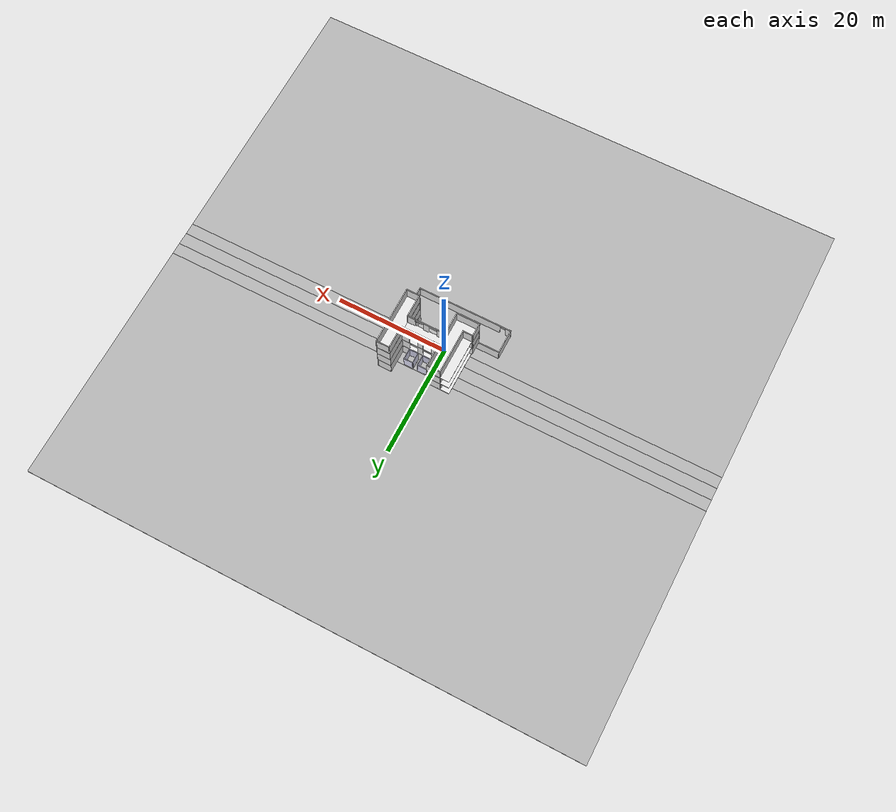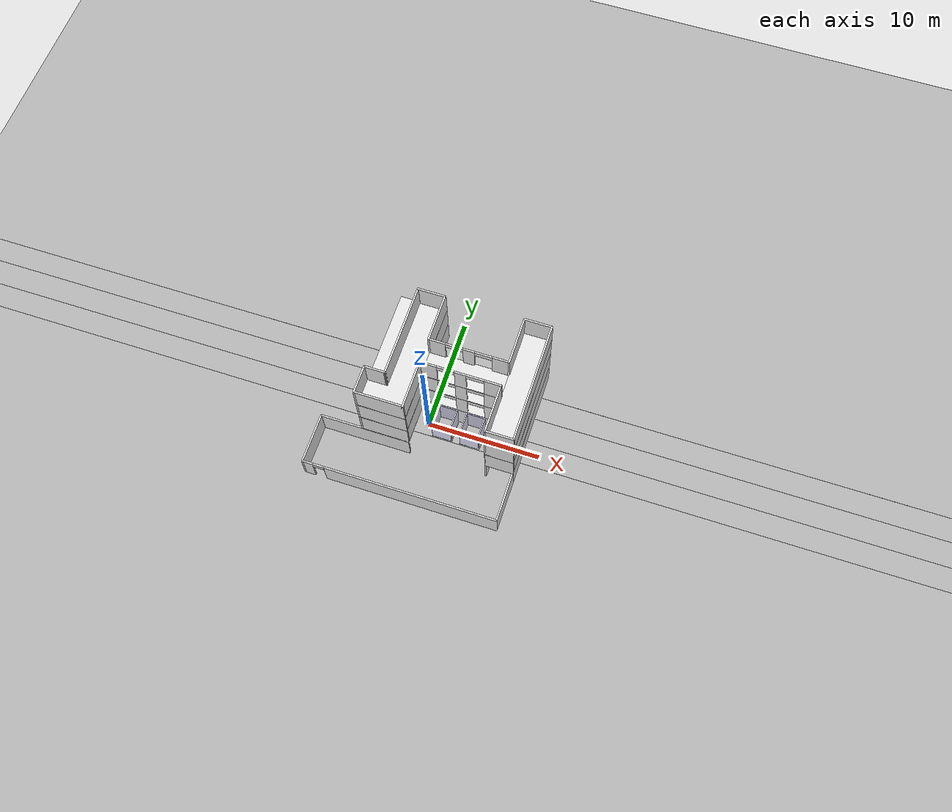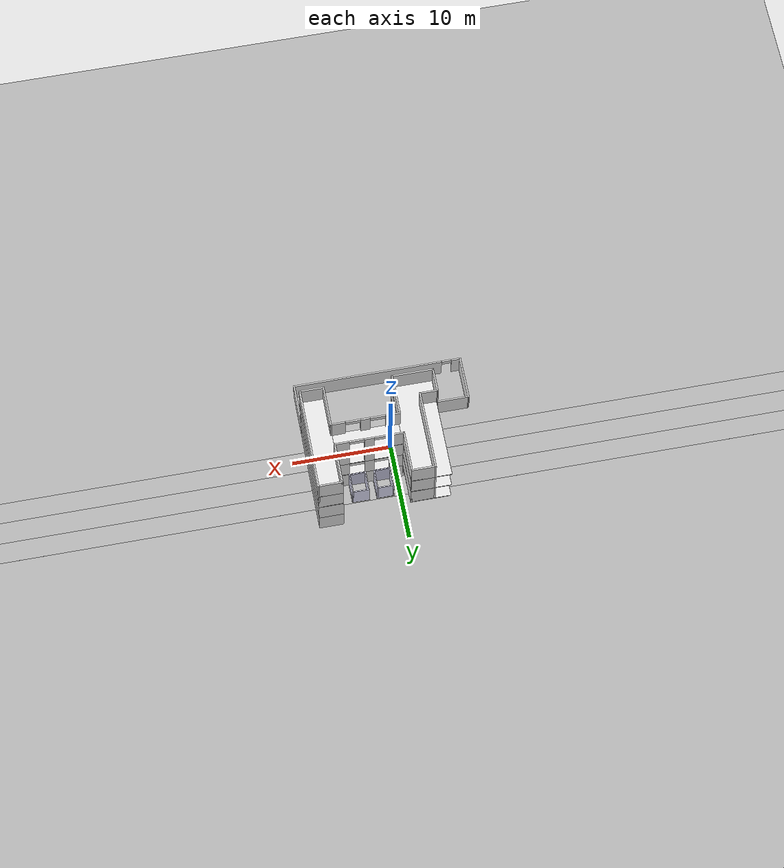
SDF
<sdf version='1.7'>
  <world name='default'>
    <plugin filename="ignition-gazebo-contact-system" name="ignition::gazebo::systems::Contact" />
    <plugin filename="ignition-gazebo-imu-system" name="ignition::gazebo::systems::Imu" />
    <plugin filename="ignition-gazebo-physics-system" name="ignition::gazebo::systems::Physics" />
    <plugin filename="ignition-gazebo-scene-broadcaster-system" name="ignition::gazebo::systems::SceneBroadcaster" />
    <plugin filename="ignition-gazebo-sensors-system" name="ignition::gazebo::systems::Sensors" />
    <plugin filename="ignition-gazebo-user-commands-system" name="ignition::gazebo::systems::UserCommands" />

    <light name='sun' type='directional'>
      <cast_shadows>1</cast_shadows>
      <pose>0 0 10 0 -0 0</pose>
      <diffuse>0.8 0.8 0.8 1</diffuse>
      <specular>0.2 0.2 0.2 1</specular>
      <attenuation>
        <range>1000</range>
        <constant>0.9</constant>
        <linear>0.01</linear>
        <quadratic>0.001</quadratic>
      </attenuation>
      <direction>-0.5 0.1 -0.9</direction>
      <spot>
        <inner_angle>0</inner_angle>
        <outer_angle>0</outer_angle>
        <falloff>0</falloff>
      </spot>
    </light>
    <model name='ground_plane'>
      <static>1</static>
      <link name='link'>
        <collision name='gnd_s_col'>
          <pose>0.000 -25.512 -0.05 0 0 0</pose>
          <geometry>
            <box>
              <size>100.000 48.975 0.1</size>
            </box>
          </geometry>
        </collision>
        <collision name='gnd_s_left_col'>
          <pose>-24.684 0.025 -0.05 0 0 0</pose>
          <geometry>
            <box>
              <size>50.632 2.100 0.1</size>
            </box>
          </geometry>
        </collision>
        <collision name='gnd_s_mid_col'>
          <pose>2.775 0.025 -0.05 0 0 0</pose>
          <geometry>
            <box>
              <size>0.686 2.100 0.1</size>
            </box>
          </geometry>
        </collision>
        <collision name='gnd_s_right_col'>
          <pose>27.459 0.025 -0.05 0 0 0</pose>
          <geometry>
            <box>
              <size>45.082 2.100 0.1</size>
            </box>
          </geometry>
        </collision>
        <collision name='gnd_mid_col'>
          <pose>0.000 2.175 -0.05 0 0 0</pose>
          <geometry>
            <box>
              <size>100.000 2.200 0.1</size>
            </box>
          </geometry>
        </collision>
        <collision name='gnd_n_left_col'>
          <pose>-24.684 4.325 -0.05 0 0 0</pose>
          <geometry>
            <box>
              <size>50.632 2.100 0.1</size>
            </box>
          </geometry>
        </collision>
        <collision name='gnd_n_mid_col'>
          <pose>2.775 4.325 -0.05 0 0 0</pose>
          <geometry>
            <box>
              <size>0.686 2.100 0.1</size>
            </box>
          </geometry>
        </collision>
        <collision name='gnd_n_right_col'>
          <pose>27.459 4.325 -0.05 0 0 0</pose>
          <geometry>
            <box>
              <size>45.082 2.100 0.1</size>
            </box>
          </geometry>
        </collision>
        <collision name='gnd_n_col'>
          <pose>0.000 27.688 -0.05 0 0 0</pose>
          <geometry>
            <box>
              <size>100.000 44.625 0.1</size>
            </box>
          </geometry>
        </collision>
        <visual name='gnd_s_vis'>
          <pose>0.000 -25.512 -0.05 0 0 0</pose>
          <geometry>
            <box>
              <size>100.000 48.975 0.1</size>
            </box>
          </geometry>
          <material>
            <ambient>0.7 0.7 0.7 1</ambient>
            <diffuse>0.7 0.7 0.7 1</diffuse>
            <specular>0.1 0.1 0.1 1</specular>
          </material>
        </visual>
        <visual name='gnd_s_left_vis'>
          <pose>-24.684 0.025 -0.05 0 0 0</pose>
          <geometry>
            <box>
              <size>50.632 2.100 0.1</size>
            </box>
          </geometry>
          <material>
            <ambient>0.7 0.7 0.7 1</ambient>
            <diffuse>0.7 0.7 0.7 1</diffuse>
            <specular>0.1 0.1 0.1 1</specular>
          </material>
        </visual>
        <visual name='gnd_s_mid_vis'>
          <pose>2.775 0.025 -0.05 0 0 0</pose>
          <geometry>
            <box>
              <size>0.686 2.100 0.1</size>
            </box>
          </geometry>
          <material>
            <ambient>0.7 0.7 0.7 1</ambient>
            <diffuse>0.7 0.7 0.7 1</diffuse>
            <specular>0.1 0.1 0.1 1</specular>
          </material>
        </visual>
        <visual name='gnd_s_right_vis'>
          <pose>27.459 0.025 -0.05 0 0 0</pose>
          <geometry>
            <box>
              <size>45.082 2.100 0.1</size>
            </box>
          </geometry>
          <material>
            <ambient>0.7 0.7 0.7 1</ambient>
            <diffuse>0.7 0.7 0.7 1</diffuse>
            <specular>0.1 0.1 0.1 1</specular>
          </material>
        </visual>
        <visual name='gnd_mid_vis'>
          <pose>0.000 2.175 -0.05 0 0 0</pose>
          <geometry>
            <box>
              <size>100.000 2.200 0.1</size>
            </box>
          </geometry>
          <material>
            <ambient>0.7 0.7 0.7 1</ambient>
            <diffuse>0.7 0.7 0.7 1</diffuse>
            <specular>0.1 0.1 0.1 1</specular>
          </material>
        </visual>
        <visual name='gnd_n_left_vis'>
          <pose>-24.684 4.325 -0.05 0 0 0</pose>
          <geometry>
            <box>
              <size>50.632 2.100 0.1</size>
            </box>
          </geometry>
          <material>
            <ambient>0.7 0.7 0.7 1</ambient>
            <diffuse>0.7 0.7 0.7 1</diffuse>
            <specular>0.1 0.1 0.1 1</specular>
          </material>
        </visual>
        <visual name='gnd_n_mid_vis'>
          <pose>2.775 4.325 -0.05 0 0 0</pose>
          <geometry>
            <box>
              <size>0.686 2.100 0.1</size>
            </box>
          </geometry>
          <material>
            <ambient>0.7 0.7 0.7 1</ambient>
            <diffuse>0.7 0.7 0.7 1</diffuse>
            <specular>0.1 0.1 0.1 1</specular>
          </material>
        </visual>
        <visual name='gnd_n_right_vis'>
          <pose>27.459 4.325 -0.05 0 0 0</pose>
          <geometry>
            <box>
              <size>45.082 2.100 0.1</size>
            </box>
          </geometry>
          <material>
            <ambient>0.7 0.7 0.7 1</ambient>
            <diffuse>0.7 0.7 0.7 1</diffuse>
            <specular>0.1 0.1 0.1 1</specular>
          </material>
        </visual>
        <visual name='gnd_n_vis'>
          <pose>0.000 27.688 -0.05 0 0 0</pose>
          <geometry>
            <box>
              <size>100.000 44.625 0.1</size>
            </box>
          </geometry>
          <material>
            <ambient>0.7 0.7 0.7 1</ambient>
            <diffuse>0.7 0.7 0.7 1</diffuse>
            <specular>0.1 0.1 0.1 1</specular>
          </material>
        </visual>
        <self_collide>0</self_collide>
        <enable_wind>0</enable_wind>
        <kinematic>0</kinematic>
      </link>
    </model>
    <gravity>0 0 -9.8</gravity>
    <magnetic_field>6e-06 2.3e-05 -4.2e-05</magnetic_field>
    <atmosphere type='adiabatic'/>
    <physics type='ode'>
      <real_time_update_rate>1000</real_time_update_rate>
      <max_step_size>0.001</max_step_size>
      <real_time_factor>1</real_time_factor>
    </physics>
    <scene>
      <ambient>0.4 0.4 0.4 1</ambient>
      <background>0.7 0.7 0.7 1</background>
      <shadows>1</shadows>
    </scene>
    <wind/>
    <spherical_coordinates>
      <surface_model>EARTH_WGS84</surface_model>
      <latitude_deg>0</latitude_deg>
      <longitude_deg>0</longitude_deg>
      <elevation>0</elevation>
      <heading_deg>0</heading_deg>
    </spherical_coordinates>
    <model name='building'>
      <pose>0 0 0 0 -0 0</pose>
      <link name='Floor_0'>
                <collision name='Floor_0_Visual_0_col'>
          <pose>7.375 2.175 0.05 0 -0 0</pose>
          <geometry>
            <box>
              <size>2.5 10.5 0.1</size>
            </box>
          </geometry>
        </collision>
        <visual name='Floor_0_Visual_0'>
          <pose>7.375 2.175 0.05 0 -0 0</pose>
          <geometry>
            <box>
              <size>2.5 10.5 0.1</size>
            </box>
          </geometry>
          <material>
            <ambient>0.9 0.9 0.9 1</ambient>
            <diffuse>0.9 0.9 0.9 1</diffuse>
            <specular>0.1 0.1 0.1 1</specular>
          </material>
          <meta>
            <layer>1</layer>
          </meta>
        </visual>
                <collision name='Floor_0_Visual_1_col'>
          <pose>-2.625 2.175 0.05 0 -0 0</pose>
          <geometry>
            <box>
              <size>4.1 10.5 0.1</size>
            </box>
          </geometry>
        </collision>
        <visual name='Floor_0_Visual_1'>
          <pose>-2.625 2.175 0.05 0 -0 0</pose>
          <geometry>
            <box>
              <size>4.1 10.5 0.1</size>
            </box>
          </geometry>
          <material>
            <ambient>0.9 0.9 0.9 1</ambient>
            <diffuse>0.9 0.9 0.9 1</diffuse>
            <specular>0.1 0.1 0.1 1</specular>
          </material>
          <meta>
            <layer>1</layer>
          </meta>
        </visual>
                <collision name='Floor_0_Visual_2_col'>
          <pose>2.775 2.175 0.05 0 -0 0</pose>
          <geometry>
            <box>
              <size>6.85 2.3 0.1</size>
            </box>
          </geometry>
        </collision>
        <visual name='Floor_0_Visual_2'>
          <pose>2.775 2.175 0.05 0 -0 0</pose>
          <geometry>
            <box>
              <size>6.85 2.3 0.1</size>
            </box>
          </geometry>
          <material>
            <ambient>0.9 0.9 0.9 1</ambient>
            <diffuse>0.9 0.9 0.9 1</diffuse>
            <specular>0.1 0.1 0.1 1</specular>
          </material>
          <meta>
            <layer>1</layer>
          </meta>
        </visual>
        <pose>0 0 2.5 0 -0 0</pose>
        <self_collide>0</self_collide>
        <enable_wind>0</enable_wind>
        <kinematic>0</kinematic>
      </link>
      <link name='Floor_1'>
                <collision name='Floor_1_Visual_0_col'>
          <pose>7.375 2.175 0.05 0 -0 0</pose>
          <geometry>
            <box>
              <size>2.5 10.5 0.1</size>
            </box>
          </geometry>
        </collision>
        <visual name='Floor_1_Visual_0'>
          <pose>7.375 2.175 0.05 0 -0 0</pose>
          <geometry>
            <box>
              <size>2.5 10.5 0.1</size>
            </box>
          </geometry>
          <material>
            <ambient>0.9 0.9 0.9 1</ambient>
            <diffuse>0.9 0.9 0.9 1</diffuse>
            <specular>0.1 0.1 0.1 1</specular>
          </material>
          <meta>
            <layer>1</layer>
          </meta>
        </visual>
                <collision name='Floor_1_Visual_1_col'>
          <pose>-2.625 2.175 0.05 0 -0 0</pose>
          <geometry>
            <box>
              <size>4.1 10.5 0.1</size>
            </box>
          </geometry>
        </collision>
        <visual name='Floor_1_Visual_1'>
          <pose>-2.625 2.175 0.05 0 -0 0</pose>
          <geometry>
            <box>
              <size>4.1 10.5 0.1</size>
            </box>
          </geometry>
          <material>
            <ambient>0.9 0.9 0.9 1</ambient>
            <diffuse>0.9 0.9 0.9 1</diffuse>
            <specular>0.1 0.1 0.1 1</specular>
          </material>
          <meta>
            <layer>1</layer>
          </meta>
        </visual>
                <collision name='Floor_1_Visual_2_col'>
          <pose>2.775 2.175 0.05 0 -0 0</pose>
          <geometry>
            <box>
              <size>6.85 2.3 0.1</size>
            </box>
          </geometry>
        </collision>
        <visual name='Floor_1_Visual_2'>
          <pose>2.775 2.175 0.05 0 -0 0</pose>
          <geometry>
            <box>
              <size>6.85 2.3 0.1</size>
            </box>
          </geometry>
          <material>
            <ambient>0.9 0.9 0.9 1</ambient>
            <diffuse>0.9 0.9 0.9 1</diffuse>
            <specular>0.1 0.1 0.1 1</specular>
          </material>
          <meta>
            <layer>1</layer>
          </meta>
        </visual>
        <pose>0 0 7.5 0 -0 0</pose>
        <self_collide>0</self_collide>
        <enable_wind>0</enable_wind>
        <kinematic>0</kinematic>
      </link>
      <link name='Floor_2'>
                <collision name='Floor_2_Visual_0_col'>
          <pose>7.375 2.175 0.05 0 -0 0</pose>
          <geometry>
            <box>
              <size>2.5 10.5 0.1</size>
            </box>
          </geometry>
        </collision>
        <visual name='Floor_2_Visual_0'>
          <pose>7.375 2.175 0.05 0 -0 0</pose>
          <geometry>
            <box>
              <size>2.5 10.5 0.1</size>
            </box>
          </geometry>
          <material>
            <ambient>0.9 0.9 0.9 1</ambient>
            <diffuse>0.9 0.9 0.9 1</diffuse>
            <specular>0.1 0.1 0.1 1</specular>
          </material>
          <meta>
            <layer>1</layer>
          </meta>
        </visual>
                <collision name='Floor_2_Visual_1_col'>
          <pose>-2.625 2.175 0.05 0 -0 0</pose>
          <geometry>
            <box>
              <size>4.1 10.5 0.1</size>
            </box>
          </geometry>
        </collision>
        <visual name='Floor_2_Visual_1'>
          <pose>-2.625 2.175 0.05 0 -0 0</pose>
          <geometry>
            <box>
              <size>4.1 10.5 0.1</size>
            </box>
          </geometry>
          <material>
            <ambient>0.9 0.9 0.9 1</ambient>
            <diffuse>0.9 0.9 0.9 1</diffuse>
            <specular>0.1 0.1 0.1 1</specular>
          </material>
          <meta>
            <layer>1</layer>
          </meta>
        </visual>
                <collision name='Floor_2_Visual_2_col'>
          <pose>2.775 2.175 0.05 0 -0 0</pose>
          <geometry>
            <box>
              <size>6.85 2.3 0.1</size>
            </box>
          </geometry>
        </collision>
        <visual name='Floor_2_Visual_2'>
          <pose>2.775 2.175 0.05 0 -0 0</pose>
          <geometry>
            <box>
              <size>6.85 2.3 0.1</size>
            </box>
          </geometry>
          <material>
            <ambient>0.9 0.9 0.9 1</ambient>
            <diffuse>0.9 0.9 0.9 1</diffuse>
            <specular>0.1 0.1 0.1 1</specular>
          </material>
          <meta>
            <layer>1</layer>
          </meta>
        </visual>
        <pose>0 0 5 0 -0 0</pose>
        <self_collide>0</self_collide>
        <enable_wind>0</enable_wind>
        <kinematic>0</kinematic>
      </link>
      <link name='Wall_100'>
                <collision name='Wall_100_Visual_col'>
          <pose>0 0 1.25 0 -0 0</pose>
          <geometry>
            <box>
              <size>4.5 0.15 2.5</size>
            </box>
          </geometry>
        </collision>
        <visual name='Wall_100_Visual'>
          <pose>0 0 1.25 0 -0 0</pose>
          <geometry>
            <box>
              <size>4.5 0.15 2.5</size>
            </box>
          </geometry>
          <material>
            <ambient>0.9 0.9 0.9 1</ambient>
            <diffuse>0.9 0.9 0.9 1</diffuse>
            <specular>0.1 0.1 0.1 1</specular>
          </material>
          <meta>
            <layer>0</layer>
          </meta>
        </visual>
        <pose>-8.55 -5.175 0 0 -0 1.5708</pose>
        <self_collide>0</self_collide>
        <enable_wind>0</enable_wind>
        <kinematic>0</kinematic>
      </link>
      <link name='Wall_101'>
                <collision name='Wall_101_Visual_col'>
          <pose>0 0 1.25 0 -0 0</pose>
          <geometry>
            <box>
              <size>8 0.15 2.5</size>
            </box>
          </geometry>
        </collision>
        <visual name='Wall_101_Visual'>
          <pose>0 0 1.25 0 -0 0</pose>
          <geometry>
            <box>
              <size>8 0.15 2.5</size>
            </box>
          </geometry>
          <material>
            <ambient>0.9 0.9 0.9 1</ambient>
            <diffuse>0.9 0.9 0.9 1</diffuse>
            <specular>0.1 0.1 0.1 1</specular>
          </material>
          <meta>
            <layer>0</layer>
          </meta>
        </visual>
        <pose>-4.625 -3 0 0 -0 0</pose>
        <self_collide>0</self_collide>
        <enable_wind>0</enable_wind>
        <kinematic>0</kinematic>
      </link>
      <link name='Wall_38'>
        <pose>2.775 3.25 0 0 -0 0</pose>
                <collision name='Wall_38_Visual_0_col'>
          <pose>-2.74441 0 1.25 0 -0 0</pose>
          <geometry>
            <box>
              <size>1.51117 0.15 2.5</size>
            </box>
          </geometry>
        </collision>
        <visual name='Wall_38_Visual_0'>
          <pose>-2.74441 0 1.25 0 -0 0</pose>
          <geometry>
            <box>
              <size>1.51117 0.15 2.5</size>
            </box>
          </geometry>
          <material>
            <ambient>0.9 0.9 0.9 1</ambient>
            <diffuse>0.9 0.9 0.9 1</diffuse>
            <specular>0.1 0.1 0.1 1</specular>
          </material>
          <meta>
            <layer>0</layer>
          </meta>
        </visual>
                <collision name='Wall_38_Visual_1_col'>
          <pose>0.004325 0 1.25 0 -0 0</pose>
          <geometry>
            <box>
              <size>0.9863 0.15 2.5</size>
            </box>
          </geometry>
        </collision>
        <visual name='Wall_38_Visual_1'>
          <pose>0.004325 0 1.25 0 -0 0</pose>
          <geometry>
            <box>
              <size>0.9863 0.15 2.5</size>
            </box>
          </geometry>
          <material>
            <ambient>0.9 0.9 0.9 1</ambient>
            <diffuse>0.9 0.9 0.9 1</diffuse>
            <specular>0.1 0.1 0.1 1</specular>
          </material>
          <meta>
            <layer>0</layer>
          </meta>
        </visual>
                <collision name='Wall_38_Visual_2_col'>
          <pose>2.74874 0 1.25 0 -0 0</pose>
          <geometry>
            <box>
              <size>1.50253 0.15 2.5</size>
            </box>
          </geometry>
        </collision>
        <visual name='Wall_38_Visual_2'>
          <pose>2.74874 0 1.25 0 -0 0</pose>
          <geometry>
            <box>
              <size>1.50253 0.15 2.5</size>
            </box>
          </geometry>
          <material>
            <ambient>0.9 0.9 0.9 1</ambient>
            <diffuse>0.9 0.9 0.9 1</diffuse>
            <specular>0.1 0.1 0.1 1</specular>
          </material>
          <meta>
            <layer>0</layer>
          </meta>
        </visual>
                <collision name='Wall_38_Visual_3_col'>
          <pose>-1.23883 0 2.25 0 -0 0</pose>
          <geometry>
            <box>
              <size>1.5 0.15 0.5</size>
            </box>
          </geometry>
        </collision>
        <visual name='Wall_38_Visual_3'>
          <pose>-1.23883 0 2.25 0 -0 0</pose>
          <geometry>
            <box>
              <size>1.5 0.15 0.5</size>
            </box>
          </geometry>
          <material>
            <ambient>0.9 0.9 0.9 1</ambient>
            <diffuse>0.9 0.9 0.9 1</diffuse>
            <specular>0.1 0.1 0.1 1</specular>
          </material>
          <meta>
            <layer>0</layer>
          </meta>
        </visual>
                <collision name='Wall_38_Visual_4_col'>
          <pose>1.24747 0 2.25 0 -0 0</pose>
          <geometry>
            <box>
              <size>1.5 0.15 0.5</size>
            </box>
          </geometry>
        </collision>
        <visual name='Wall_38_Visual_4'>
          <pose>1.24747 0 2.25 0 -0 0</pose>
          <geometry>
            <box>
              <size>1.5 0.15 0.5</size>
            </box>
          </geometry>
          <material>
            <ambient>0.9 0.9 0.9 1</ambient>
            <diffuse>0.9 0.9 0.9 1</diffuse>
            <specular>0.1 0.1 0.1 1</specular>
          </material>
          <meta>
            <layer>0</layer>
          </meta>
        </visual>
        <self_collide>0</self_collide>
        <enable_wind>0</enable_wind>
        <kinematic>0</kinematic>
      </link>
      <link name='Wall_39'>
                <collision name='Wall_39_Visual_col'>
          <pose>0 0 1.25 0 -0 0</pose>
          <geometry>
            <box>
              <size>4.25 0.15 2.5</size>
            </box>
          </geometry>
        </collision>
        <visual name='Wall_39_Visual'>
          <pose>0 0 1.25 0 -0 0</pose>
          <geometry>
            <box>
              <size>4.25 0.15 2.5</size>
            </box>
          </geometry>
          <material>
            <ambient>0.9 0.9 0.9 1</ambient>
            <diffuse>0.9 0.9 0.9 1</diffuse>
            <specular>0.1 0.1 0.1 1</specular>
          </material>
          <meta>
            <layer>0</layer>
          </meta>
        </visual>
        <pose>6.2 5.3 0 0 -0 1.5708</pose>
        <self_collide>0</self_collide>
        <enable_wind>0</enable_wind>
        <kinematic>0</kinematic>
      </link>
      <link name='Wall_40'>
                <collision name='Wall_40_Visual_col'>
          <pose>0 0 1.25 0 -0 0</pose>
          <geometry>
            <box>
              <size>2.5 0.15 2.5</size>
            </box>
          </geometry>
        </collision>
        <visual name='Wall_40_Visual'>
          <pose>0 0 1.25 0 -0 0</pose>
          <geometry>
            <box>
              <size>2.5 0.15 2.5</size>
            </box>
          </geometry>
          <material>
            <ambient>0.9 0.9 0.9 1</ambient>
            <diffuse>0.9 0.9 0.9 1</diffuse>
            <specular>0.1 0.1 0.1 1</specular>
          </material>
          <meta>
            <layer>0</layer>
          </meta>
        </visual>
        <pose>7.375 7.35 0 0 -0 0</pose>
        <self_collide>0</self_collide>
        <enable_wind>0</enable_wind>
        <kinematic>0</kinematic>
      </link>
      <link name='Wall_41'>
                <collision name='Wall_41_Visual_col'>
          <pose>0 0 1.25 0 -0 0</pose>
          <geometry>
            <box>
              <size>10.5 0.15 2.5</size>
            </box>
          </geometry>
        </collision>
        <visual name='Wall_41_Visual'>
          <pose>0 0 1.25 0 -0 0</pose>
          <geometry>
            <box>
              <size>10.5 0.15 2.5</size>
            </box>
          </geometry>
          <material>
            <ambient>0.9 0.9 0.9 1</ambient>
            <diffuse>0.9 0.9 0.9 1</diffuse>
            <specular>0.1 0.1 0.1 1</specular>
          </material>
          <meta>
            <layer>0</layer>
          </meta>
        </visual>
        <pose>8.55 2.175 0 0 -0 -1.5708</pose>
        <self_collide>0</self_collide>
        <enable_wind>0</enable_wind>
        <kinematic>0</kinematic>
      </link>
      <link name='Wall_43'>
                <collision name='Wall_43_Visual_col'>
          <pose>0 0 1.25 0 -0 0</pose>
          <geometry>
            <box>
              <size>4.25 0.15 2.5</size>
            </box>
          </geometry>
        </collision>
        <visual name='Wall_43_Visual'>
          <pose>0 0 1.25 0 -0 0</pose>
          <geometry>
            <box>
              <size>4.25 0.15 2.5</size>
            </box>
          </geometry>
          <material>
            <ambient>0.9 0.9 0.9 1</ambient>
            <diffuse>0.9 0.9 0.9 1</diffuse>
            <specular>0.1 0.1 0.1 1</specular>
          </material>
          <meta>
            <layer>0</layer>
          </meta>
        </visual>
        <pose>6.2 -0.95 0 0 -0 1.5708</pose>
        <self_collide>0</self_collide>
        <enable_wind>0</enable_wind>
        <kinematic>0</kinematic>
      </link>
      <link name='Wall_44'>
        <pose>2.775 1.1 0 0 -0 3.14159</pose>
                <collision name='Wall_44_Visual_0_col'>
          <pose>-2.74874 0 1.25 0 -0 0</pose>
          <geometry>
            <box>
              <size>1.50253 0.15 2.5</size>
            </box>
          </geometry>
        </collision>
        <visual name='Wall_44_Visual_0'>
          <pose>-2.74874 0 1.25 0 -0 0</pose>
          <geometry>
            <box>
              <size>1.50253 0.15 2.5</size>
            </box>
          </geometry>
          <material>
            <ambient>0.9 0.9 0.9 1</ambient>
            <diffuse>0.9 0.9 0.9 1</diffuse>
            <specular>0.1 0.1 0.1 1</specular>
          </material>
          <meta>
            <layer>0</layer>
          </meta>
        </visual>
                <collision name='Wall_44_Visual_1_col'>
          <pose>-0.004325 0 1.25 0 -0 0</pose>
          <geometry>
            <box>
              <size>0.9863 0.15 2.5</size>
            </box>
          </geometry>
        </collision>
        <visual name='Wall_44_Visual_1'>
          <pose>-0.004325 0 1.25 0 -0 0</pose>
          <geometry>
            <box>
              <size>0.9863 0.15 2.5</size>
            </box>
          </geometry>
          <material>
            <ambient>0.9 0.9 0.9 1</ambient>
            <diffuse>0.9 0.9 0.9 1</diffuse>
            <specular>0.1 0.1 0.1 1</specular>
          </material>
          <meta>
            <layer>0</layer>
          </meta>
        </visual>
                <collision name='Wall_44_Visual_2_col'>
          <pose>2.74441 0 1.25 0 -0 0</pose>
          <geometry>
            <box>
              <size>1.51117 0.15 2.5</size>
            </box>
          </geometry>
        </collision>
        <visual name='Wall_44_Visual_2'>
          <pose>2.74441 0 1.25 0 -0 0</pose>
          <geometry>
            <box>
              <size>1.51117 0.15 2.5</size>
            </box>
          </geometry>
          <material>
            <ambient>0.9 0.9 0.9 1</ambient>
            <diffuse>0.9 0.9 0.9 1</diffuse>
            <specular>0.1 0.1 0.1 1</specular>
          </material>
          <meta>
            <layer>0</layer>
          </meta>
        </visual>
                <collision name='Wall_44_Visual_3_col'>
          <pose>-1.24747 0 2.25 0 -0 0</pose>
          <geometry>
            <box>
              <size>1.5 0.15 0.5</size>
            </box>
          </geometry>
        </collision>
        <visual name='Wall_44_Visual_3'>
          <pose>-1.24747 0 2.25 0 -0 0</pose>
          <geometry>
            <box>
              <size>1.5 0.15 0.5</size>
            </box>
          </geometry>
          <material>
            <ambient>0.9 0.9 0.9 1</ambient>
            <diffuse>0.9 0.9 0.9 1</diffuse>
            <specular>0.1 0.1 0.1 1</specular>
          </material>
          <meta>
            <layer>0</layer>
          </meta>
        </visual>
                <collision name='Wall_44_Visual_4_col'>
          <pose>1.23883 0 2.25 0 -0 0</pose>
          <geometry>
            <box>
              <size>1.5 0.15 0.5</size>
            </box>
          </geometry>
        </collision>
        <visual name='Wall_44_Visual_4'>
          <pose>1.23883 0 2.25 0 -0 0</pose>
          <geometry>
            <box>
              <size>1.5 0.15 0.5</size>
            </box>
          </geometry>
          <material>
            <ambient>0.9 0.9 0.9 1</ambient>
            <diffuse>0.9 0.9 0.9 1</diffuse>
            <specular>0.1 0.1 0.1 1</specular>
          </material>
          <meta>
            <layer>0</layer>
          </meta>
        </visual>
        <self_collide>0</self_collide>
        <enable_wind>0</enable_wind>
        <kinematic>0</kinematic>
      </link>
      <link name='Wall_54'>
                <collision name='Wall_54_Visual_col'>
          <pose>0 0 1.25 0 -0 0</pose>
          <geometry>
            <box>
              <size>2.5 0.15 2.5</size>
            </box>
          </geometry>
        </collision>
        <visual name='Wall_54_Visual'>
          <pose>0 0 1.25 0 -0 0</pose>
          <geometry>
            <box>
              <size>2.5 0.15 2.5</size>
            </box>
          </geometry>
          <material>
            <ambient>0.9 0.9 0.9 1</ambient>
            <diffuse>0.9 0.9 0.9 1</diffuse>
            <specular>0.1 0.1 0.1 1</specular>
          </material>
          <meta>
            <layer>1</layer>
          </meta>
        </visual>
        <pose>-1.825 7.35 2.5 0 -0 0</pose>
        <self_collide>0</self_collide>
        <enable_wind>0</enable_wind>
        <kinematic>0</kinematic>
      </link>
      <link name='Wall_55'>
                <collision name='Wall_55_Visual_col'>
          <pose>0 0 1.25 0 -0 0</pose>
          <geometry>
            <box>
              <size>4.25 0.15 2.5</size>
            </box>
          </geometry>
        </collision>
        <visual name='Wall_55_Visual'>
          <pose>0 0 1.25 0 -0 0</pose>
          <geometry>
            <box>
              <size>4.25 0.15 2.5</size>
            </box>
          </geometry>
          <material>
            <ambient>0.9 0.9 0.9 1</ambient>
            <diffuse>0.9 0.9 0.9 1</diffuse>
            <specular>0.1 0.1 0.1 1</specular>
          </material>
          <meta>
            <layer>1</layer>
          </meta>
        </visual>
        <pose>-0.65 5.3 2.5 0 -0 -1.5708</pose>
        <self_collide>0</self_collide>
        <enable_wind>0</enable_wind>
        <kinematic>0</kinematic>
      </link>
      <link name='Wall_56'>
        <pose>2.775 3.25 2.5 0 -0 0</pose>
                <collision name='Wall_56_Visual_0_col'>
          <pose>-2.74441 0 1.25 0 -0 0</pose>
          <geometry>
            <box>
              <size>1.51117 0.15 2.5</size>
            </box>
          </geometry>
        </collision>
        <visual name='Wall_56_Visual_0'>
          <pose>-2.74441 0 1.25 0 -0 0</pose>
          <geometry>
            <box>
              <size>1.51117 0.15 2.5</size>
            </box>
          </geometry>
          <material>
            <ambient>0.9 0.9 0.9 1</ambient>
            <diffuse>0.9 0.9 0.9 1</diffuse>
            <specular>0.1 0.1 0.1 1</specular>
          </material>
          <meta>
            <layer>1</layer>
          </meta>
        </visual>
                <collision name='Wall_56_Visual_1_col'>
          <pose>0.004325 0 1.25 0 -0 0</pose>
          <geometry>
            <box>
              <size>0.9863 0.15 2.5</size>
            </box>
          </geometry>
        </collision>
        <visual name='Wall_56_Visual_1'>
          <pose>0.004325 0 1.25 0 -0 0</pose>
          <geometry>
            <box>
              <size>0.9863 0.15 2.5</size>
            </box>
          </geometry>
          <material>
            <ambient>0.9 0.9 0.9 1</ambient>
            <diffuse>0.9 0.9 0.9 1</diffuse>
            <specular>0.1 0.1 0.1 1</specular>
          </material>
          <meta>
            <layer>1</layer>
          </meta>
        </visual>
                <collision name='Wall_56_Visual_2_col'>
          <pose>2.74874 0 1.25 0 -0 0</pose>
          <geometry>
            <box>
              <size>1.50253 0.15 2.5</size>
            </box>
          </geometry>
        </collision>
        <visual name='Wall_56_Visual_2'>
          <pose>2.74874 0 1.25 0 -0 0</pose>
          <geometry>
            <box>
              <size>1.50253 0.15 2.5</size>
            </box>
          </geometry>
          <material>
            <ambient>0.9 0.9 0.9 1</ambient>
            <diffuse>0.9 0.9 0.9 1</diffuse>
            <specular>0.1 0.1 0.1 1</specular>
          </material>
          <meta>
            <layer>1</layer>
          </meta>
        </visual>
                <collision name='Wall_56_Visual_3_col'>
          <pose>-1.23883 0 2.25 0 -0 0</pose>
          <geometry>
            <box>
              <size>1.5 0.15 0.5</size>
            </box>
          </geometry>
        </collision>
        <visual name='Wall_56_Visual_3'>
          <pose>-1.23883 0 2.25 0 -0 0</pose>
          <geometry>
            <box>
              <size>1.5 0.15 0.5</size>
            </box>
          </geometry>
          <material>
            <ambient>0.9 0.9 0.9 1</ambient>
            <diffuse>0.9 0.9 0.9 1</diffuse>
            <specular>0.1 0.1 0.1 1</specular>
          </material>
          <meta>
            <layer>1</layer>
          </meta>
        </visual>
                <collision name='Wall_56_Visual_4_col'>
          <pose>1.24747 0 2.25 0 -0 0</pose>
          <geometry>
            <box>
              <size>1.5 0.15 0.5</size>
            </box>
          </geometry>
        </collision>
        <visual name='Wall_56_Visual_4'>
          <pose>1.24747 0 2.25 0 -0 0</pose>
          <geometry>
            <box>
              <size>1.5 0.15 0.5</size>
            </box>
          </geometry>
          <material>
            <ambient>0.9 0.9 0.9 1</ambient>
            <diffuse>0.9 0.9 0.9 1</diffuse>
            <specular>0.1 0.1 0.1 1</specular>
          </material>
          <meta>
            <layer>1</layer>
          </meta>
        </visual>
        <self_collide>0</self_collide>
        <enable_wind>0</enable_wind>
        <kinematic>0</kinematic>
      </link>
      <link name='Wall_57'>
                <collision name='Wall_57_Visual_col'>
          <pose>0 0 1.25 0 -0 0</pose>
          <geometry>
            <box>
              <size>4.25 0.15 2.5</size>
            </box>
          </geometry>
        </collision>
        <visual name='Wall_57_Visual'>
          <pose>0 0 1.25 0 -0 0</pose>
          <geometry>
            <box>
              <size>4.25 0.15 2.5</size>
            </box>
          </geometry>
          <material>
            <ambient>0.9 0.9 0.9 1</ambient>
            <diffuse>0.9 0.9 0.9 1</diffuse>
            <specular>0.1 0.1 0.1 1</specular>
          </material>
          <meta>
            <layer>1</layer>
          </meta>
        </visual>
        <pose>6.2 5.3 2.5 0 -0 1.5708</pose>
        <self_collide>0</self_collide>
        <enable_wind>0</enable_wind>
        <kinematic>0</kinematic>
      </link>
      <link name='Wall_58'>
                <collision name='Wall_58_Visual_col'>
          <pose>0 0 1.25 0 -0 0</pose>
          <geometry>
            <box>
              <size>2.5 0.15 2.5</size>
            </box>
          </geometry>
        </collision>
        <visual name='Wall_58_Visual'>
          <pose>0 0 1.25 0 -0 0</pose>
          <geometry>
            <box>
              <size>2.5 0.15 2.5</size>
            </box>
          </geometry>
          <material>
            <ambient>0.9 0.9 0.9 1</ambient>
            <diffuse>0.9 0.9 0.9 1</diffuse>
            <specular>0.1 0.1 0.1 1</specular>
          </material>
          <meta>
            <layer>1</layer>
          </meta>
        </visual>
        <pose>7.375 7.35 2.5 0 -0 0</pose>
        <self_collide>0</self_collide>
        <enable_wind>0</enable_wind>
        <kinematic>0</kinematic>
      </link>
      <link name='Wall_59'>
                <collision name='Wall_59_Visual_col'>
          <pose>0 0 1.25 0 -0 0</pose>
          <geometry>
            <box>
              <size>10.5 0.15 2.5</size>
            </box>
          </geometry>
        </collision>
        <visual name='Wall_59_Visual'>
          <pose>0 0 1.25 0 -0 0</pose>
          <geometry>
            <box>
              <size>10.5 0.15 2.5</size>
            </box>
          </geometry>
          <material>
            <ambient>0.9 0.9 0.9 1</ambient>
            <diffuse>0.9 0.9 0.9 1</diffuse>
            <specular>0.1 0.1 0.1 1</specular>
          </material>
          <meta>
            <layer>1</layer>
          </meta>
        </visual>
        <pose>8.55 2.175 2.5 0 -0 -1.5708</pose>
        <self_collide>0</self_collide>
        <enable_wind>0</enable_wind>
        <kinematic>0</kinematic>
      </link>
      <link name='Wall_60'>
                <collision name='Wall_60_Visual_col'>
          <pose>0 0 1.25 0 -0 0</pose>
          <geometry>
            <box>
              <size>2.5 0.15 2.5</size>
            </box>
          </geometry>
        </collision>
        <visual name='Wall_60_Visual'>
          <pose>0 0 1.25 0 -0 0</pose>
          <geometry>
            <box>
              <size>2.5 0.15 2.5</size>
            </box>
          </geometry>
          <material>
            <ambient>0.9 0.9 0.9 1</ambient>
            <diffuse>0.9 0.9 0.9 1</diffuse>
            <specular>0.1 0.1 0.1 1</specular>
          </material>
          <meta>
            <layer>1</layer>
          </meta>
        </visual>
        <pose>7.375 -3 2.5 0 -0 3.14159</pose>
        <self_collide>0</self_collide>
        <enable_wind>0</enable_wind>
        <kinematic>0</kinematic>
      </link>
      <link name='Wall_61'>
                <collision name='Wall_61_Visual_col'>
          <pose>0 0 1.25 0 -0 0</pose>
          <geometry>
            <box>
              <size>4.25 0.15 2.5</size>
            </box>
          </geometry>
        </collision>
        <visual name='Wall_61_Visual'>
          <pose>0 0 1.25 0 -0 0</pose>
          <geometry>
            <box>
              <size>4.25 0.15 2.5</size>
            </box>
          </geometry>
          <material>
            <ambient>0.9 0.9 0.9 1</ambient>
            <diffuse>0.9 0.9 0.9 1</diffuse>
            <specular>0.1 0.1 0.1 1</specular>
          </material>
          <meta>
            <layer>1</layer>
          </meta>
        </visual>
        <pose>6.2 -0.95 2.5 0 -0 1.5708</pose>
        <self_collide>0</self_collide>
        <enable_wind>0</enable_wind>
        <kinematic>0</kinematic>
      </link>
      <link name='Wall_62'>
        <pose>2.775 1.1 2.5 0 -0 3.14159</pose>
                <collision name='Wall_62_Visual_0_col'>
          <pose>-2.74874 0 1.25 0 -0 0</pose>
          <geometry>
            <box>
              <size>1.50253 0.15 2.5</size>
            </box>
          </geometry>
        </collision>
        <visual name='Wall_62_Visual_0'>
          <pose>-2.74874 0 1.25 0 -0 0</pose>
          <geometry>
            <box>
              <size>1.50253 0.15 2.5</size>
            </box>
          </geometry>
          <material>
            <ambient>0.9 0.9 0.9 1</ambient>
            <diffuse>0.9 0.9 0.9 1</diffuse>
            <specular>0.1 0.1 0.1 1</specular>
          </material>
          <meta>
            <layer>1</layer>
          </meta>
        </visual>
                <collision name='Wall_62_Visual_1_col'>
          <pose>-0.004325 0 1.25 0 -0 0</pose>
          <geometry>
            <box>
              <size>0.9863 0.15 2.5</size>
            </box>
          </geometry>
        </collision>
        <visual name='Wall_62_Visual_1'>
          <pose>-0.004325 0 1.25 0 -0 0</pose>
          <geometry>
            <box>
              <size>0.9863 0.15 2.5</size>
            </box>
          </geometry>
          <material>
            <ambient>0.9 0.9 0.9 1</ambient>
            <diffuse>0.9 0.9 0.9 1</diffuse>
            <specular>0.1 0.1 0.1 1</specular>
          </material>
          <meta>
            <layer>1</layer>
          </meta>
        </visual>
                <collision name='Wall_62_Visual_2_col'>
          <pose>2.74441 0 1.25 0 -0 0</pose>
          <geometry>
            <box>
              <size>1.51117 0.15 2.5</size>
            </box>
          </geometry>
        </collision>
        <visual name='Wall_62_Visual_2'>
          <pose>2.74441 0 1.25 0 -0 0</pose>
          <geometry>
            <box>
              <size>1.51117 0.15 2.5</size>
            </box>
          </geometry>
          <material>
            <ambient>0.9 0.9 0.9 1</ambient>
            <diffuse>0.9 0.9 0.9 1</diffuse>
            <specular>0.1 0.1 0.1 1</specular>
          </material>
          <meta>
            <layer>1</layer>
          </meta>
        </visual>
                <collision name='Wall_62_Visual_3_col'>
          <pose>-1.24747 0 2.25 0 -0 0</pose>
          <geometry>
            <box>
              <size>1.5 0.15 0.5</size>
            </box>
          </geometry>
        </collision>
        <visual name='Wall_62_Visual_3'>
          <pose>-1.24747 0 2.25 0 -0 0</pose>
          <geometry>
            <box>
              <size>1.5 0.15 0.5</size>
            </box>
          </geometry>
          <material>
            <ambient>0.9 0.9 0.9 1</ambient>
            <diffuse>0.9 0.9 0.9 1</diffuse>
            <specular>0.1 0.1 0.1 1</specular>
          </material>
          <meta>
            <layer>1</layer>
          </meta>
        </visual>
                <collision name='Wall_62_Visual_4_col'>
          <pose>1.23883 0 2.25 0 -0 0</pose>
          <geometry>
            <box>
              <size>1.5 0.15 0.5</size>
            </box>
          </geometry>
        </collision>
        <visual name='Wall_62_Visual_4'>
          <pose>1.23883 0 2.25 0 -0 0</pose>
          <geometry>
            <box>
              <size>1.5 0.15 0.5</size>
            </box>
          </geometry>
          <material>
            <ambient>0.9 0.9 0.9 1</ambient>
            <diffuse>0.9 0.9 0.9 1</diffuse>
            <specular>0.1 0.1 0.1 1</specular>
          </material>
          <meta>
            <layer>1</layer>
          </meta>
        </visual>
        <self_collide>0</self_collide>
        <enable_wind>0</enable_wind>
        <kinematic>0</kinematic>
      </link>
      <link name='Wall_63'>
                <collision name='Wall_63_Visual_col'>
          <pose>0 0 1.25 0 -0 0</pose>
          <geometry>
            <box>
              <size>4.25 0.15 2.5</size>
            </box>
          </geometry>
        </collision>
        <visual name='Wall_63_Visual'>
          <pose>0 0 1.25 0 -0 0</pose>
          <geometry>
            <box>
              <size>4.25 0.15 2.5</size>
            </box>
          </geometry>
          <material>
            <ambient>0.9 0.9 0.9 1</ambient>
            <diffuse>0.9 0.9 0.9 1</diffuse>
            <specular>0.1 0.1 0.1 1</specular>
          </material>
          <meta>
            <layer>1</layer>
          </meta>
        </visual>
        <pose>-0.65 -0.95 2.5 0 -0 -1.5708</pose>
        <self_collide>0</self_collide>
        <enable_wind>0</enable_wind>
        <kinematic>0</kinematic>
      </link>
      <link name='Wall_64'>
                <collision name='Wall_64_Visual_col'>
          <pose>0 0 1.25 0 -0 0</pose>
          <geometry>
            <box>
              <size>4.25 0.15 2.5</size>
            </box>
          </geometry>
        </collision>
        <visual name='Wall_64_Visual'>
          <pose>0 0 1.25 0 -0 0</pose>
          <geometry>
            <box>
              <size>4.25 0.15 2.5</size>
            </box>
          </geometry>
          <material>
            <ambient>0.9 0.9 0.9 1</ambient>
            <diffuse>0.9 0.9 0.9 1</diffuse>
            <specular>0.1 0.1 0.1 1</specular>
          </material>
          <meta>
            <layer>1</layer>
          </meta>
        </visual>
        <pose>-2.7 -3 2.5 0 -0 3.14159</pose>
        <self_collide>0</self_collide>
        <enable_wind>0</enable_wind>
        <kinematic>0</kinematic>
      </link>
      <link name='Wall_65'>
                <collision name='Wall_65_Visual_col'>
          <pose>0 0 1.25 0 -0 0</pose>
          <geometry>
            <box>
              <size>2.5 0.15 2.5</size>
            </box>
          </geometry>
        </collision>
        <visual name='Wall_65_Visual'>
          <pose>0 0 1.25 0 -0 0</pose>
          <geometry>
            <box>
              <size>2.5 0.15 2.5</size>
            </box>
          </geometry>
          <material>
            <ambient>0.9 0.9 0.9 1</ambient>
            <diffuse>0.9 0.9 0.9 1</diffuse>
            <specular>0.1 0.1 0.1 1</specular>
          </material>
          <meta>
            <layer>1</layer>
          </meta>
        </visual>
        <pose>-4.75 -1.825 2.5 0 -0 1.5708</pose>
        <self_collide>0</self_collide>
        <enable_wind>0</enable_wind>
        <kinematic>0</kinematic>
      </link>
      <link name='Wall_66'>
                <collision name='Wall_66_Visual_col'>
          <pose>0 0 1.25 0 -0 0</pose>
          <geometry>
            <box>
              <size>1.9 0.15 2.5</size>
            </box>
          </geometry>
        </collision>
        <visual name='Wall_66_Visual'>
          <pose>0 0 1.25 0 -0 0</pose>
          <geometry>
            <box>
              <size>1.9 0.15 2.5</size>
            </box>
          </geometry>
          <material>
            <ambient>0.9 0.9 0.9 1</ambient>
            <diffuse>0.9 0.9 0.9 1</diffuse>
            <specular>0.1 0.1 0.1 1</specular>
          </material>
          <meta>
            <layer>1</layer>
          </meta>
        </visual>
        <pose>-3.875 -0.650563 2.5 0 -0 -0.000643</pose>
        <self_collide>0</self_collide>
        <enable_wind>0</enable_wind>
        <kinematic>0</kinematic>
      </link>
      <link name='Wall_67'>
                <collision name='Wall_67_Visual_col'>
          <pose>0 0 1.25 0 -0 0</pose>
          <geometry>
            <box>
              <size>8.15113 0.15 2.5</size>
            </box>
          </geometry>
        </collision>
        <visual name='Wall_67_Visual'>
          <pose>0 0 1.25 0 -0 0</pose>
          <geometry>
            <box>
              <size>8.15113 0.15 2.5</size>
            </box>
          </geometry>
          <material>
            <ambient>0.9 0.9 0.9 1</ambient>
            <diffuse>0.9 0.9 0.9 1</diffuse>
            <specular>0.1 0.1 0.1 1</specular>
          </material>
          <meta>
            <layer>1</layer>
          </meta>
        </visual>
        <pose>-3 3.34944 2.5 0 -0 1.5708</pose>
        <self_collide>0</self_collide>
        <enable_wind>0</enable_wind>
        <kinematic>0</kinematic>
      </link>
      <link name='Wall_68'>
                <collision name='Wall_68_Visual_col'>
          <pose>0 0 1.25 0 -0 0</pose>
          <geometry>
            <box>
              <size>2.5 0.15 2.5</size>
            </box>
          </geometry>
        </collision>
        <visual name='Wall_68_Visual'>
          <pose>0 0 1.25 0 -0 0</pose>
          <geometry>
            <box>
              <size>2.5 0.15 2.5</size>
            </box>
          </geometry>
          <material>
            <ambient>0.9 0.9 0.9 1</ambient>
            <diffuse>0.9 0.9 0.9 1</diffuse>
            <specular>0.1 0.1 0.1 1</specular>
          </material>
          <meta>
            <layer>2</layer>
          </meta>
        </visual>
        <pose>-1.825 7.35 5 0 -0 0</pose>
        <self_collide>0</self_collide>
        <enable_wind>0</enable_wind>
        <kinematic>0</kinematic>
      </link>
      <link name='Wall_69'>
                <collision name='Wall_69_Visual_col'>
          <pose>0 0 1.25 0 -0 0</pose>
          <geometry>
            <box>
              <size>4.25 0.15 2.5</size>
            </box>
          </geometry>
        </collision>
        <visual name='Wall_69_Visual'>
          <pose>0 0 1.25 0 -0 0</pose>
          <geometry>
            <box>
              <size>4.25 0.15 2.5</size>
            </box>
          </geometry>
          <material>
            <ambient>0.9 0.9 0.9 1</ambient>
            <diffuse>0.9 0.9 0.9 1</diffuse>
            <specular>0.1 0.1 0.1 1</specular>
          </material>
          <meta>
            <layer>2</layer>
          </meta>
        </visual>
        <pose>-0.65 5.3 5 0 -0 -1.5708</pose>
        <self_collide>0</self_collide>
        <enable_wind>0</enable_wind>
        <kinematic>0</kinematic>
      </link>
      <link name='Wall_70'>
        <pose>2.775 3.25 5 0 -0 0</pose>
                <collision name='Wall_70_Visual_0_col'>
          <pose>-2.74441 0 1.25 0 -0 0</pose>
          <geometry>
            <box>
              <size>1.51117 0.15 2.5</size>
            </box>
          </geometry>
        </collision>
        <visual name='Wall_70_Visual_0'>
          <pose>-2.74441 0 1.25 0 -0 0</pose>
          <geometry>
            <box>
              <size>1.51117 0.15 2.5</size>
            </box>
          </geometry>
          <material>
            <ambient>0.9 0.9 0.9 1</ambient>
            <diffuse>0.9 0.9 0.9 1</diffuse>
            <specular>0.1 0.1 0.1 1</specular>
          </material>
          <meta>
            <layer>2</layer>
          </meta>
        </visual>
                <collision name='Wall_70_Visual_1_col'>
          <pose>0.004325 0 1.25 0 -0 0</pose>
          <geometry>
            <box>
              <size>0.9863 0.15 2.5</size>
            </box>
          </geometry>
        </collision>
        <visual name='Wall_70_Visual_1'>
          <pose>0.004325 0 1.25 0 -0 0</pose>
          <geometry>
            <box>
              <size>0.9863 0.15 2.5</size>
            </box>
          </geometry>
          <material>
            <ambient>0.9 0.9 0.9 1</ambient>
            <diffuse>0.9 0.9 0.9 1</diffuse>
            <specular>0.1 0.1 0.1 1</specular>
          </material>
          <meta>
            <layer>2</layer>
          </meta>
        </visual>
                <collision name='Wall_70_Visual_2_col'>
          <pose>2.74874 0 1.25 0 -0 0</pose>
          <geometry>
            <box>
              <size>1.50253 0.15 2.5</size>
            </box>
          </geometry>
        </collision>
        <visual name='Wall_70_Visual_2'>
          <pose>2.74874 0 1.25 0 -0 0</pose>
          <geometry>
            <box>
              <size>1.50253 0.15 2.5</size>
            </box>
          </geometry>
          <material>
            <ambient>0.9 0.9 0.9 1</ambient>
            <diffuse>0.9 0.9 0.9 1</diffuse>
            <specular>0.1 0.1 0.1 1</specular>
          </material>
          <meta>
            <layer>2</layer>
          </meta>
        </visual>
                <collision name='Wall_70_Visual_3_col'>
          <pose>-1.23883 0 2.25 0 -0 0</pose>
          <geometry>
            <box>
              <size>1.5 0.15 0.5</size>
            </box>
          </geometry>
        </collision>
        <visual name='Wall_70_Visual_3'>
          <pose>-1.23883 0 2.25 0 -0 0</pose>
          <geometry>
            <box>
              <size>1.5 0.15 0.5</size>
            </box>
          </geometry>
          <material>
            <ambient>0.9 0.9 0.9 1</ambient>
            <diffuse>0.9 0.9 0.9 1</diffuse>
            <specular>0.1 0.1 0.1 1</specular>
          </material>
          <meta>
            <layer>2</layer>
          </meta>
        </visual>
                <collision name='Wall_70_Visual_4_col'>
          <pose>1.24747 0 2.25 0 -0 0</pose>
          <geometry>
            <box>
              <size>1.5 0.15 0.5</size>
            </box>
          </geometry>
        </collision>
        <visual name='Wall_70_Visual_4'>
          <pose>1.24747 0 2.25 0 -0 0</pose>
          <geometry>
            <box>
              <size>1.5 0.15 0.5</size>
            </box>
          </geometry>
          <material>
            <ambient>0.9 0.9 0.9 1</ambient>
            <diffuse>0.9 0.9 0.9 1</diffuse>
            <specular>0.1 0.1 0.1 1</specular>
          </material>
          <meta>
            <layer>2</layer>
          </meta>
        </visual>
        <self_collide>0</self_collide>
        <enable_wind>0</enable_wind>
        <kinematic>0</kinematic>
      </link>
      <link name='Wall_71'>
                <collision name='Wall_71_Visual_col'>
          <pose>0 0 1.25 0 -0 0</pose>
          <geometry>
            <box>
              <size>4.25 0.15 2.5</size>
            </box>
          </geometry>
        </collision>
        <visual name='Wall_71_Visual'>
          <pose>0 0 1.25 0 -0 0</pose>
          <geometry>
            <box>
              <size>4.25 0.15 2.5</size>
            </box>
          </geometry>
          <material>
            <ambient>0.9 0.9 0.9 1</ambient>
            <diffuse>0.9 0.9 0.9 1</diffuse>
            <specular>0.1 0.1 0.1 1</specular>
          </material>
          <meta>
            <layer>2</layer>
          </meta>
        </visual>
        <pose>6.2 5.3 5 0 -0 1.5708</pose>
        <self_collide>0</self_collide>
        <enable_wind>0</enable_wind>
        <kinematic>0</kinematic>
      </link>
      <link name='Wall_72'>
                <collision name='Wall_72_Visual_col'>
          <pose>0 0 1.25 0 -0 0</pose>
          <geometry>
            <box>
              <size>2.5 0.15 2.5</size>
            </box>
          </geometry>
        </collision>
        <visual name='Wall_72_Visual'>
          <pose>0 0 1.25 0 -0 0</pose>
          <geometry>
            <box>
              <size>2.5 0.15 2.5</size>
            </box>
          </geometry>
          <material>
            <ambient>0.9 0.9 0.9 1</ambient>
            <diffuse>0.9 0.9 0.9 1</diffuse>
            <specular>0.1 0.1 0.1 1</specular>
          </material>
          <meta>
            <layer>2</layer>
          </meta>
        </visual>
        <pose>7.375 7.35 5 0 -0 0</pose>
        <self_collide>0</self_collide>
        <enable_wind>0</enable_wind>
        <kinematic>0</kinematic>
      </link>
      <link name='Wall_73'>
                <collision name='Wall_73_Visual_col'>
          <pose>0 0 1.25 0 -0 0</pose>
          <geometry>
            <box>
              <size>10.5 0.15 2.5</size>
            </box>
          </geometry>
        </collision>
        <visual name='Wall_73_Visual'>
          <pose>0 0 1.25 0 -0 0</pose>
          <geometry>
            <box>
              <size>10.5 0.15 2.5</size>
            </box>
          </geometry>
          <material>
            <ambient>0.9 0.9 0.9 1</ambient>
            <diffuse>0.9 0.9 0.9 1</diffuse>
            <specular>0.1 0.1 0.1 1</specular>
          </material>
          <meta>
            <layer>2</layer>
          </meta>
        </visual>
        <pose>8.55 2.175 5 0 -0 -1.5708</pose>
        <self_collide>0</self_collide>
        <enable_wind>0</enable_wind>
        <kinematic>0</kinematic>
      </link>
      <link name='Wall_74'>
                <collision name='Wall_74_Visual_col'>
          <pose>0 0 1.25 0 -0 0</pose>
          <geometry>
            <box>
              <size>2.5 0.15 2.5</size>
            </box>
          </geometry>
        </collision>
        <visual name='Wall_74_Visual'>
          <pose>0 0 1.25 0 -0 0</pose>
          <geometry>
            <box>
              <size>2.5 0.15 2.5</size>
            </box>
          </geometry>
          <material>
            <ambient>0.9 0.9 0.9 1</ambient>
            <diffuse>0.9 0.9 0.9 1</diffuse>
            <specular>0.1 0.1 0.1 1</specular>
          </material>
          <meta>
            <layer>2</layer>
          </meta>
        </visual>
        <pose>7.375 -3 5 0 -0 3.14159</pose>
        <self_collide>0</self_collide>
        <enable_wind>0</enable_wind>
        <kinematic>0</kinematic>
      </link>
      <link name='Wall_75'>
                <collision name='Wall_75_Visual_col'>
          <pose>0 0 1.25 0 -0 0</pose>
          <geometry>
            <box>
              <size>4.25 0.15 2.5</size>
            </box>
          </geometry>
        </collision>
        <visual name='Wall_75_Visual'>
          <pose>0 0 1.25 0 -0 0</pose>
          <geometry>
            <box>
              <size>4.25 0.15 2.5</size>
            </box>
          </geometry>
          <material>
            <ambient>0.9 0.9 0.9 1</ambient>
            <diffuse>0.9 0.9 0.9 1</diffuse>
            <specular>0.1 0.1 0.1 1</specular>
          </material>
          <meta>
            <layer>2</layer>
          </meta>
        </visual>
        <pose>6.2 -0.95 5 0 -0 1.5708</pose>
        <self_collide>0</self_collide>
        <enable_wind>0</enable_wind>
        <kinematic>0</kinematic>
      </link>
      <link name='Wall_76'>
        <pose>2.775 1.1 5 0 -0 3.14159</pose>
                <collision name='Wall_76_Visual_0_col'>
          <pose>-2.74874 0 1.25 0 -0 0</pose>
          <geometry>
            <box>
              <size>1.50253 0.15 2.5</size>
            </box>
          </geometry>
        </collision>
        <visual name='Wall_76_Visual_0'>
          <pose>-2.74874 0 1.25 0 -0 0</pose>
          <geometry>
            <box>
              <size>1.50253 0.15 2.5</size>
            </box>
          </geometry>
          <material>
            <ambient>0.9 0.9 0.9 1</ambient>
            <diffuse>0.9 0.9 0.9 1</diffuse>
            <specular>0.1 0.1 0.1 1</specular>
          </material>
          <meta>
            <layer>2</layer>
          </meta>
        </visual>
                <collision name='Wall_76_Visual_1_col'>
          <pose>-0.004325 0 1.25 0 -0 0</pose>
          <geometry>
            <box>
              <size>0.9863 0.15 2.5</size>
            </box>
          </geometry>
        </collision>
        <visual name='Wall_76_Visual_1'>
          <pose>-0.004325 0 1.25 0 -0 0</pose>
          <geometry>
            <box>
              <size>0.9863 0.15 2.5</size>
            </box>
          </geometry>
          <material>
            <ambient>0.9 0.9 0.9 1</ambient>
            <diffuse>0.9 0.9 0.9 1</diffuse>
            <specular>0.1 0.1 0.1 1</specular>
          </material>
          <meta>
            <layer>2</layer>
          </meta>
        </visual>
                <collision name='Wall_76_Visual_2_col'>
          <pose>2.74441 0 1.25 0 -0 0</pose>
          <geometry>
            <box>
              <size>1.51117 0.15 2.5</size>
            </box>
          </geometry>
        </collision>
        <visual name='Wall_76_Visual_2'>
          <pose>2.74441 0 1.25 0 -0 0</pose>
          <geometry>
            <box>
              <size>1.51117 0.15 2.5</size>
            </box>
          </geometry>
          <material>
            <ambient>0.9 0.9 0.9 1</ambient>
            <diffuse>0.9 0.9 0.9 1</diffuse>
            <specular>0.1 0.1 0.1 1</specular>
          </material>
          <meta>
            <layer>2</layer>
          </meta>
        </visual>
                <collision name='Wall_76_Visual_3_col'>
          <pose>-1.24747 0 2.25 0 -0 0</pose>
          <geometry>
            <box>
              <size>1.5 0.15 0.5</size>
            </box>
          </geometry>
        </collision>
        <visual name='Wall_76_Visual_3'>
          <pose>-1.24747 0 2.25 0 -0 0</pose>
          <geometry>
            <box>
              <size>1.5 0.15 0.5</size>
            </box>
          </geometry>
          <material>
            <ambient>0.9 0.9 0.9 1</ambient>
            <diffuse>0.9 0.9 0.9 1</diffuse>
            <specular>0.1 0.1 0.1 1</specular>
          </material>
          <meta>
            <layer>2</layer>
          </meta>
        </visual>
                <collision name='Wall_76_Visual_4_col'>
          <pose>1.23883 0 2.25 0 -0 0</pose>
          <geometry>
            <box>
              <size>1.5 0.15 0.5</size>
            </box>
          </geometry>
        </collision>
        <visual name='Wall_76_Visual_4'>
          <pose>1.23883 0 2.25 0 -0 0</pose>
          <geometry>
            <box>
              <size>1.5 0.15 0.5</size>
            </box>
          </geometry>
          <material>
            <ambient>0.9 0.9 0.9 1</ambient>
            <diffuse>0.9 0.9 0.9 1</diffuse>
            <specular>0.1 0.1 0.1 1</specular>
          </material>
          <meta>
            <layer>2</layer>
          </meta>
        </visual>
        <self_collide>0</self_collide>
        <enable_wind>0</enable_wind>
        <kinematic>0</kinematic>
      </link>
      <link name='Wall_77'>
                <collision name='Wall_77_Visual_col'>
          <pose>0 0 1.25 0 -0 0</pose>
          <geometry>
            <box>
              <size>4.25 0.15 2.5</size>
            </box>
          </geometry>
        </collision>
        <visual name='Wall_77_Visual'>
          <pose>0 0 1.25 0 -0 0</pose>
          <geometry>
            <box>
              <size>4.25 0.15 2.5</size>
            </box>
          </geometry>
          <material>
            <ambient>0.9 0.9 0.9 1</ambient>
            <diffuse>0.9 0.9 0.9 1</diffuse>
            <specular>0.1 0.1 0.1 1</specular>
          </material>
          <meta>
            <layer>2</layer>
          </meta>
        </visual>
        <pose>-0.65 -0.95 5 0 -0 -1.5708</pose>
        <self_collide>0</self_collide>
        <enable_wind>0</enable_wind>
        <kinematic>0</kinematic>
      </link>
      <link name='Wall_78'>
                <collision name='Wall_78_Visual_col'>
          <pose>0 0 1.25 0 -0 0</pose>
          <geometry>
            <box>
              <size>4.25 0.15 2.5</size>
            </box>
          </geometry>
        </collision>
        <visual name='Wall_78_Visual'>
          <pose>0 0 1.25 0 -0 0</pose>
          <geometry>
            <box>
              <size>4.25 0.15 2.5</size>
            </box>
          </geometry>
          <material>
            <ambient>0.9 0.9 0.9 1</ambient>
            <diffuse>0.9 0.9 0.9 1</diffuse>
            <specular>0.1 0.1 0.1 1</specular>
          </material>
          <meta>
            <layer>2</layer>
          </meta>
        </visual>
        <pose>-2.7 -3 5 0 -0 3.14159</pose>
        <self_collide>0</self_collide>
        <enable_wind>0</enable_wind>
        <kinematic>0</kinematic>
      </link>
      <link name='Wall_79'>
                <collision name='Wall_79_Visual_col'>
          <pose>0 0 1.25 0 -0 0</pose>
          <geometry>
            <box>
              <size>2.5 0.15 2.5</size>
            </box>
          </geometry>
        </collision>
        <visual name='Wall_79_Visual'>
          <pose>0 0 1.25 0 -0 0</pose>
          <geometry>
            <box>
              <size>2.5 0.15 2.5</size>
            </box>
          </geometry>
          <material>
            <ambient>0.9 0.9 0.9 1</ambient>
            <diffuse>0.9 0.9 0.9 1</diffuse>
            <specular>0.1 0.1 0.1 1</specular>
          </material>
          <meta>
            <layer>2</layer>
          </meta>
        </visual>
        <pose>-4.75 -1.825 5 0 -0 1.5708</pose>
        <self_collide>0</self_collide>
        <enable_wind>0</enable_wind>
        <kinematic>0</kinematic>
      </link>
      <link name='Wall_80'>
                <collision name='Wall_80_Visual_col'>
          <pose>0 0 1.25 0 -0 0</pose>
          <geometry>
            <box>
              <size>1.9 0.15 2.5</size>
            </box>
          </geometry>
        </collision>
        <visual name='Wall_80_Visual'>
          <pose>0 0 1.25 0 -0 0</pose>
          <geometry>
            <box>
              <size>1.9 0.15 2.5</size>
            </box>
          </geometry>
          <material>
            <ambient>0.9 0.9 0.9 1</ambient>
            <diffuse>0.9 0.9 0.9 1</diffuse>
            <specular>0.1 0.1 0.1 1</specular>
          </material>
          <meta>
            <layer>2</layer>
          </meta>
        </visual>
        <pose>-3.875 -0.650563 5 0 -0 -0.000643</pose>
        <self_collide>0</self_collide>
        <enable_wind>0</enable_wind>
        <kinematic>0</kinematic>
      </link>
      <link name='Wall_81'>
                <collision name='Wall_81_Visual_col'>
          <pose>0 0 1.25 0 -0 0</pose>
          <geometry>
            <box>
              <size>8.15113 0.15 2.5</size>
            </box>
          </geometry>
        </collision>
        <visual name='Wall_81_Visual'>
          <pose>0 0 1.25 0 -0 0</pose>
          <geometry>
            <box>
              <size>8.15113 0.15 2.5</size>
            </box>
          </geometry>
          <material>
            <ambient>0.9 0.9 0.9 1</ambient>
            <diffuse>0.9 0.9 0.9 1</diffuse>
            <specular>0.1 0.1 0.1 1</specular>
          </material>
          <meta>
            <layer>2</layer>
          </meta>
        </visual>
        <pose>-3 3.34944 5 0 -0 1.5708</pose>
        <self_collide>0</self_collide>
        <enable_wind>0</enable_wind>
        <kinematic>0</kinematic>
      </link>
      <link name='Wall_82'>
                <collision name='Wall_82_Visual_col'>
          <pose>0 0 1.25 0 -0 0</pose>
          <geometry>
            <box>
              <size>2.5 0.15 2.5</size>
            </box>
          </geometry>
        </collision>
        <visual name='Wall_82_Visual'>
          <pose>0 0 1.25 0 -0 0</pose>
          <geometry>
            <box>
              <size>2.5 0.15 2.5</size>
            </box>
          </geometry>
          <material>
            <ambient>0.9 0.9 0.9 1</ambient>
            <diffuse>0.9 0.9 0.9 1</diffuse>
            <specular>0.1 0.1 0.1 1</specular>
          </material>
          <meta>
            <layer>3</layer>
          </meta>
        </visual>
        <pose>-1.825 7.35 7.5 0 -0 0</pose>
        <self_collide>0</self_collide>
        <enable_wind>0</enable_wind>
        <kinematic>0</kinematic>
      </link>
      <link name='Wall_83'>
                <collision name='Wall_83_Visual_col'>
          <pose>0 0 1.25 0 -0 0</pose>
          <geometry>
            <box>
              <size>4.25 0.15 2.5</size>
            </box>
          </geometry>
        </collision>
        <visual name='Wall_83_Visual'>
          <pose>0 0 1.25 0 -0 0</pose>
          <geometry>
            <box>
              <size>4.25 0.15 2.5</size>
            </box>
          </geometry>
          <material>
            <ambient>0.9 0.9 0.9 1</ambient>
            <diffuse>0.9 0.9 0.9 1</diffuse>
            <specular>0.1 0.1 0.1 1</specular>
          </material>
          <meta>
            <layer>3</layer>
          </meta>
        </visual>
        <pose>-0.65 5.3 7.5 0 -0 -1.5708</pose>
        <self_collide>0</self_collide>
        <enable_wind>0</enable_wind>
        <kinematic>0</kinematic>
      </link>
      <link name='Wall_84'>
        <pose>2.775 3.25 7.5 0 -0 0</pose>
                <collision name='Wall_84_Visual_0_col'>
          <pose>-2.74441 0 1.25 0 -0 0</pose>
          <geometry>
            <box>
              <size>1.51117 0.15 2.5</size>
            </box>
          </geometry>
        </collision>
        <visual name='Wall_84_Visual_0'>
          <pose>-2.74441 0 1.25 0 -0 0</pose>
          <geometry>
            <box>
              <size>1.51117 0.15 2.5</size>
            </box>
          </geometry>
          <material>
            <ambient>0.9 0.9 0.9 1</ambient>
            <diffuse>0.9 0.9 0.9 1</diffuse>
            <specular>0.1 0.1 0.1 1</specular>
          </material>
          <meta>
            <layer>3</layer>
          </meta>
        </visual>
                <collision name='Wall_84_Visual_1_col'>
          <pose>0.004325 0 1.25 0 -0 0</pose>
          <geometry>
            <box>
              <size>0.9863 0.15 2.5</size>
            </box>
          </geometry>
        </collision>
        <visual name='Wall_84_Visual_1'>
          <pose>0.004325 0 1.25 0 -0 0</pose>
          <geometry>
            <box>
              <size>0.9863 0.15 2.5</size>
            </box>
          </geometry>
          <material>
            <ambient>0.9 0.9 0.9 1</ambient>
            <diffuse>0.9 0.9 0.9 1</diffuse>
            <specular>0.1 0.1 0.1 1</specular>
          </material>
          <meta>
            <layer>3</layer>
          </meta>
        </visual>
                <collision name='Wall_84_Visual_2_col'>
          <pose>2.74874 0 1.25 0 -0 0</pose>
          <geometry>
            <box>
              <size>1.50253 0.15 2.5</size>
            </box>
          </geometry>
        </collision>
        <visual name='Wall_84_Visual_2'>
          <pose>2.74874 0 1.25 0 -0 0</pose>
          <geometry>
            <box>
              <size>1.50253 0.15 2.5</size>
            </box>
          </geometry>
          <material>
            <ambient>0.9 0.9 0.9 1</ambient>
            <diffuse>0.9 0.9 0.9 1</diffuse>
            <specular>0.1 0.1 0.1 1</specular>
          </material>
          <meta>
            <layer>3</layer>
          </meta>
        </visual>
                <collision name='Wall_84_Visual_3_col'>
          <pose>-1.23883 0 2.25 0 -0 0</pose>
          <geometry>
            <box>
              <size>1.5 0.15 0.5</size>
            </box>
          </geometry>
        </collision>
        <visual name='Wall_84_Visual_3'>
          <pose>-1.23883 0 2.25 0 -0 0</pose>
          <geometry>
            <box>
              <size>1.5 0.15 0.5</size>
            </box>
          </geometry>
          <material>
            <ambient>0.9 0.9 0.9 1</ambient>
            <diffuse>0.9 0.9 0.9 1</diffuse>
            <specular>0.1 0.1 0.1 1</specular>
          </material>
          <meta>
            <layer>3</layer>
          </meta>
        </visual>
                <collision name='Wall_84_Visual_4_col'>
          <pose>1.24747 0 2.25 0 -0 0</pose>
          <geometry>
            <box>
              <size>1.5 0.15 0.5</size>
            </box>
          </geometry>
        </collision>
        <visual name='Wall_84_Visual_4'>
          <pose>1.24747 0 2.25 0 -0 0</pose>
          <geometry>
            <box>
              <size>1.5 0.15 0.5</size>
            </box>
          </geometry>
          <material>
            <ambient>0.9 0.9 0.9 1</ambient>
            <diffuse>0.9 0.9 0.9 1</diffuse>
            <specular>0.1 0.1 0.1 1</specular>
          </material>
          <meta>
            <layer>3</layer>
          </meta>
        </visual>
        <self_collide>0</self_collide>
        <enable_wind>0</enable_wind>
        <kinematic>0</kinematic>
      </link>
      <link name='Wall_85'>
                <collision name='Wall_85_Visual_col'>
          <pose>0 0 1.25 0 -0 0</pose>
          <geometry>
            <box>
              <size>4.25 0.15 2.5</size>
            </box>
          </geometry>
        </collision>
        <visual name='Wall_85_Visual'>
          <pose>0 0 1.25 0 -0 0</pose>
          <geometry>
            <box>
              <size>4.25 0.15 2.5</size>
            </box>
          </geometry>
          <material>
            <ambient>0.9 0.9 0.9 1</ambient>
            <diffuse>0.9 0.9 0.9 1</diffuse>
            <specular>0.1 0.1 0.1 1</specular>
          </material>
          <meta>
            <layer>3</layer>
          </meta>
        </visual>
        <pose>6.2 5.3 7.5 0 -0 1.5708</pose>
        <self_collide>0</self_collide>
        <enable_wind>0</enable_wind>
        <kinematic>0</kinematic>
      </link>
      <link name='Wall_86'>
                <collision name='Wall_86_Visual_col'>
          <pose>0 0 1.25 0 -0 0</pose>
          <geometry>
            <box>
              <size>2.5 0.15 2.5</size>
            </box>
          </geometry>
        </collision>
        <visual name='Wall_86_Visual'>
          <pose>0 0 1.25 0 -0 0</pose>
          <geometry>
            <box>
              <size>2.5 0.15 2.5</size>
            </box>
          </geometry>
          <material>
            <ambient>0.9 0.9 0.9 1</ambient>
            <diffuse>0.9 0.9 0.9 1</diffuse>
            <specular>0.1 0.1 0.1 1</specular>
          </material>
          <meta>
            <layer>3</layer>
          </meta>
        </visual>
        <pose>7.375 7.35 7.5 0 -0 0</pose>
        <self_collide>0</self_collide>
        <enable_wind>0</enable_wind>
        <kinematic>0</kinematic>
      </link>
      <link name='Wall_87'>
                <collision name='Wall_87_Visual_col'>
          <pose>0 0 1.25 0 -0 0</pose>
          <geometry>
            <box>
              <size>10.5 0.15 2.5</size>
            </box>
          </geometry>
        </collision>
        <visual name='Wall_87_Visual'>
          <pose>0 0 1.25 0 -0 0</pose>
          <geometry>
            <box>
              <size>10.5 0.15 2.5</size>
            </box>
          </geometry>
          <material>
            <ambient>0.9 0.9 0.9 1</ambient>
            <diffuse>0.9 0.9 0.9 1</diffuse>
            <specular>0.1 0.1 0.1 1</specular>
          </material>
          <meta>
            <layer>3</layer>
          </meta>
        </visual>
        <pose>8.55 2.175 7.5 0 -0 -1.5708</pose>
        <self_collide>0</self_collide>
        <enable_wind>0</enable_wind>
        <kinematic>0</kinematic>
      </link>
      <link name='Wall_88'>
                <collision name='Wall_88_Visual_col'>
          <pose>0 0 1.25 0 -0 0</pose>
          <geometry>
            <box>
              <size>2.5 0.15 2.5</size>
            </box>
          </geometry>
        </collision>
        <visual name='Wall_88_Visual'>
          <pose>0 0 1.25 0 -0 0</pose>
          <geometry>
            <box>
              <size>2.5 0.15 2.5</size>
            </box>
          </geometry>
          <material>
            <ambient>0.9 0.9 0.9 1</ambient>
            <diffuse>0.9 0.9 0.9 1</diffuse>
            <specular>0.1 0.1 0.1 1</specular>
          </material>
          <meta>
            <layer>3</layer>
          </meta>
        </visual>
        <pose>7.375 -3 7.5 0 -0 3.14159</pose>
        <self_collide>0</self_collide>
        <enable_wind>0</enable_wind>
        <kinematic>0</kinematic>
      </link>
      <link name='Wall_89'>
                <collision name='Wall_89_Visual_col'>
          <pose>0 0 1.25 0 -0 0</pose>
          <geometry>
            <box>
              <size>4.25 0.15 2.5</size>
            </box>
          </geometry>
        </collision>
        <visual name='Wall_89_Visual'>
          <pose>0 0 1.25 0 -0 0</pose>
          <geometry>
            <box>
              <size>4.25 0.15 2.5</size>
            </box>
          </geometry>
          <material>
            <ambient>0.9 0.9 0.9 1</ambient>
            <diffuse>0.9 0.9 0.9 1</diffuse>
            <specular>0.1 0.1 0.1 1</specular>
          </material>
          <meta>
            <layer>3</layer>
          </meta>
        </visual>
        <pose>6.2 -0.95 7.5 0 -0 1.5708</pose>
        <self_collide>0</self_collide>
        <enable_wind>0</enable_wind>
        <kinematic>0</kinematic>
      </link>
      <link name='Wall_90'>
        <pose>2.775 1.1 7.5 0 -0 3.14159</pose>
                <collision name='Wall_90_Visual_0_col'>
          <pose>-2.74874 0 1.25 0 -0 0</pose>
          <geometry>
            <box>
              <size>1.50253 0.15 2.5</size>
            </box>
          </geometry>
        </collision>
        <visual name='Wall_90_Visual_0'>
          <pose>-2.74874 0 1.25 0 -0 0</pose>
          <geometry>
            <box>
              <size>1.50253 0.15 2.5</size>
            </box>
          </geometry>
          <material>
            <ambient>0.9 0.9 0.9 1</ambient>
            <diffuse>0.9 0.9 0.9 1</diffuse>
            <specular>0.1 0.1 0.1 1</specular>
          </material>
          <meta>
            <layer>3</layer>
          </meta>
        </visual>
                <collision name='Wall_90_Visual_1_col'>
          <pose>-0.004325 0 1.25 0 -0 0</pose>
          <geometry>
            <box>
              <size>0.9863 0.15 2.5</size>
            </box>
          </geometry>
        </collision>
        <visual name='Wall_90_Visual_1'>
          <pose>-0.004325 0 1.25 0 -0 0</pose>
          <geometry>
            <box>
              <size>0.9863 0.15 2.5</size>
            </box>
          </geometry>
          <material>
            <ambient>0.9 0.9 0.9 1</ambient>
            <diffuse>0.9 0.9 0.9 1</diffuse>
            <specular>0.1 0.1 0.1 1</specular>
          </material>
          <meta>
            <layer>3</layer>
          </meta>
        </visual>
                <collision name='Wall_90_Visual_2_col'>
          <pose>2.74441 0 1.25 0 -0 0</pose>
          <geometry>
            <box>
              <size>1.51117 0.15 2.5</size>
            </box>
          </geometry>
        </collision>
        <visual name='Wall_90_Visual_2'>
          <pose>2.74441 0 1.25 0 -0 0</pose>
          <geometry>
            <box>
              <size>1.51117 0.15 2.5</size>
            </box>
          </geometry>
          <material>
            <ambient>0.9 0.9 0.9 1</ambient>
            <diffuse>0.9 0.9 0.9 1</diffuse>
            <specular>0.1 0.1 0.1 1</specular>
          </material>
          <meta>
            <layer>3</layer>
          </meta>
        </visual>
                <collision name='Wall_90_Visual_3_col'>
          <pose>-1.24747 0 2.25 0 -0 0</pose>
          <geometry>
            <box>
              <size>1.5 0.15 0.5</size>
            </box>
          </geometry>
        </collision>
        <visual name='Wall_90_Visual_3'>
          <pose>-1.24747 0 2.25 0 -0 0</pose>
          <geometry>
            <box>
              <size>1.5 0.15 0.5</size>
            </box>
          </geometry>
          <material>
            <ambient>0.9 0.9 0.9 1</ambient>
            <diffuse>0.9 0.9 0.9 1</diffuse>
            <specular>0.1 0.1 0.1 1</specular>
          </material>
          <meta>
            <layer>3</layer>
          </meta>
        </visual>
                <collision name='Wall_90_Visual_4_col'>
          <pose>1.23883 0 2.25 0 -0 0</pose>
          <geometry>
            <box>
              <size>1.5 0.15 0.5</size>
            </box>
          </geometry>
        </collision>
        <visual name='Wall_90_Visual_4'>
          <pose>1.23883 0 2.25 0 -0 0</pose>
          <geometry>
            <box>
              <size>1.5 0.15 0.5</size>
            </box>
          </geometry>
          <material>
            <ambient>0.9 0.9 0.9 1</ambient>
            <diffuse>0.9 0.9 0.9 1</diffuse>
            <specular>0.1 0.1 0.1 1</specular>
          </material>
          <meta>
            <layer>3</layer>
          </meta>
        </visual>
        <self_collide>0</self_collide>
        <enable_wind>0</enable_wind>
        <kinematic>0</kinematic>
      </link>
      <link name='Wall_91'>
                <collision name='Wall_91_Visual_col'>
          <pose>0 0 1.25 0 -0 0</pose>
          <geometry>
            <box>
              <size>4.25 0.15 2.5</size>
            </box>
          </geometry>
        </collision>
        <visual name='Wall_91_Visual'>
          <pose>0 0 1.25 0 -0 0</pose>
          <geometry>
            <box>
              <size>4.25 0.15 2.5</size>
            </box>
          </geometry>
          <material>
            <ambient>0.9 0.9 0.9 1</ambient>
            <diffuse>0.9 0.9 0.9 1</diffuse>
            <specular>0.1 0.1 0.1 1</specular>
          </material>
          <meta>
            <layer>3</layer>
          </meta>
        </visual>
        <pose>-0.65 -0.95 7.5 0 -0 -1.5708</pose>
        <self_collide>0</self_collide>
        <enable_wind>0</enable_wind>
        <kinematic>0</kinematic>
      </link>
      <link name='Wall_92'>
                <collision name='Wall_92_Visual_col'>
          <pose>0 0 1.25 0 -0 0</pose>
          <geometry>
            <box>
              <size>4.25 0.15 2.5</size>
            </box>
          </geometry>
        </collision>
        <visual name='Wall_92_Visual'>
          <pose>0 0 1.25 0 -0 0</pose>
          <geometry>
            <box>
              <size>4.25 0.15 2.5</size>
            </box>
          </geometry>
          <material>
            <ambient>0.9 0.9 0.9 1</ambient>
            <diffuse>0.9 0.9 0.9 1</diffuse>
            <specular>0.1 0.1 0.1 1</specular>
          </material>
          <meta>
            <layer>3</layer>
          </meta>
        </visual>
        <pose>-2.7 -3 7.5 0 -0 3.14159</pose>
        <self_collide>0</self_collide>
        <enable_wind>0</enable_wind>
        <kinematic>0</kinematic>
      </link>
      <link name='Wall_93'>
                <collision name='Wall_93_Visual_col'>
          <pose>0 0 1.25 0 -0 0</pose>
          <geometry>
            <box>
              <size>2.5 0.15 2.5</size>
            </box>
          </geometry>
        </collision>
        <visual name='Wall_93_Visual'>
          <pose>0 0 1.25 0 -0 0</pose>
          <geometry>
            <box>
              <size>2.5 0.15 2.5</size>
            </box>
          </geometry>
          <material>
            <ambient>0.9 0.9 0.9 1</ambient>
            <diffuse>0.9 0.9 0.9 1</diffuse>
            <specular>0.1 0.1 0.1 1</specular>
          </material>
          <meta>
            <layer>3</layer>
          </meta>
        </visual>
        <pose>-4.75 -1.825 7.5 0 -0 1.5708</pose>
        <self_collide>0</self_collide>
        <enable_wind>0</enable_wind>
        <kinematic>0</kinematic>
      </link>
      <link name='Wall_94'>
                <collision name='Wall_94_Visual_col'>
          <pose>0 0 1.25 0 -0 0</pose>
          <geometry>
            <box>
              <size>1.9 0.15 2.5</size>
            </box>
          </geometry>
        </collision>
        <visual name='Wall_94_Visual'>
          <pose>0 0 1.25 0 -0 0</pose>
          <geometry>
            <box>
              <size>1.9 0.15 2.5</size>
            </box>
          </geometry>
          <material>
            <ambient>0.9 0.9 0.9 1</ambient>
            <diffuse>0.9 0.9 0.9 1</diffuse>
            <specular>0.1 0.1 0.1 1</specular>
          </material>
          <meta>
            <layer>3</layer>
          </meta>
        </visual>
        <pose>-3.875 -0.650563 7.5 0 -0 -0.000643</pose>
        <self_collide>0</self_collide>
        <enable_wind>0</enable_wind>
        <kinematic>0</kinematic>
      </link>
      <link name='Wall_95'>
                <collision name='Wall_95_Visual_col'>
          <pose>0 0 1.25 0 -0 0</pose>
          <geometry>
            <box>
              <size>8.15113 0.15 2.5</size>
            </box>
          </geometry>
        </collision>
        <visual name='Wall_95_Visual'>
          <pose>0 0 1.25 0 -0 0</pose>
          <geometry>
            <box>
              <size>8.15113 0.15 2.5</size>
            </box>
          </geometry>
          <material>
            <ambient>0.9 0.9 0.9 1</ambient>
            <diffuse>0.9 0.9 0.9 1</diffuse>
            <specular>0.1 0.1 0.1 1</specular>
          </material>
          <meta>
            <layer>3</layer>
          </meta>
        </visual>
        <pose>-3 3.34944 7.5 0 -0 1.5708</pose>
        <self_collide>0</self_collide>
        <enable_wind>0</enable_wind>
        <kinematic>0</kinematic>
      </link>
      <link name='Wall_96'>
                <collision name='Wall_96_Visual_col'>
          <pose>0 0 1.25 0 -0 0</pose>
          <geometry>
            <box>
              <size>2.3 0.15 2.5</size>
            </box>
          </geometry>
        </collision>
        <visual name='Wall_96_Visual'>
          <pose>0 0 1.25 0 -0 0</pose>
          <geometry>
            <box>
              <size>2.3 0.15 2.5</size>
            </box>
          </geometry>
          <material>
            <ambient>0.9 0.9 0.9 1</ambient>
            <diffuse>0.9 0.9 0.9 1</diffuse>
            <specular>0.1 0.1 0.1 1</specular>
          </material>
          <meta>
            <layer>0</layer>
          </meta>
        </visual>
        <pose>-0.65 2.175 0 0 -0 1.5708</pose>
        <self_collide>0</self_collide>
        <enable_wind>0</enable_wind>
        <kinematic>0</kinematic>
      </link>
      <link name='Wall_98'>
                <collision name='Wall_98_Visual_col'>
          <pose>0 0 1.25 0 -0 0</pose>
          <geometry>
            <box>
              <size>4.5 0.15 2.5</size>
            </box>
          </geometry>
        </collision>
        <visual name='Wall_98_Visual'>
          <pose>0 0 1.25 0 -0 0</pose>
          <geometry>
            <box>
              <size>4.5 0.15 2.5</size>
            </box>
          </geometry>
          <material>
            <ambient>0.9 0.9 0.9 1</ambient>
            <diffuse>0.9 0.9 0.9 1</diffuse>
            <specular>0.1 0.1 0.1 1</specular>
          </material>
          <meta>
            <layer>0</layer>
          </meta>
        </visual>
        <pose>8.55 -5.175 0 0 -0 -1.5708</pose>
        <self_collide>0</self_collide>
        <enable_wind>0</enable_wind>
        <kinematic>0</kinematic>
      </link>
      <link name='Wall_99'>
        <pose>-0 -7.35 0 0 -0 3.14159</pose>
                <collision name='Wall_99_Visual_0_col'>
          <pose>-0.997588 0 1.25 0 -0 0</pose>
          <geometry>
            <box>
              <size>15.2548 0.15 2.5</size>
            </box>
          </geometry>
        </collision>
        <visual name='Wall_99_Visual_0'>
          <pose>-0.997588 0 1.25 0 -0 0</pose>
          <geometry>
            <box>
              <size>15.2548 0.15 2.5</size>
            </box>
          </geometry>
          <material>
            <ambient>0.9 0.9 0.9 1</ambient>
            <diffuse>0.9 0.9 0.9 1</diffuse>
            <specular>0.1 0.1 0.1 1</specular>
          </material>
          <meta>
            <layer>0</layer>
          </meta>
        </visual>
                <collision name='Wall_99_Visual_1_col'>
          <pose>8.12741 0 1.25 0 -0 0</pose>
          <geometry>
            <box>
              <size>0.995176 0.15 2.5</size>
            </box>
          </geometry>
        </collision>
        <visual name='Wall_99_Visual_1'>
          <pose>8.12741 0 1.25 0 -0 0</pose>
          <geometry>
            <box>
              <size>0.995176 0.15 2.5</size>
            </box>
          </geometry>
          <material>
            <ambient>0.9 0.9 0.9 1</ambient>
            <diffuse>0.9 0.9 0.9 1</diffuse>
            <specular>0.1 0.1 0.1 1</specular>
          </material>
          <meta>
            <layer>0</layer>
          </meta>
        </visual>
                <collision name='Wall_99_Visual_2_col'>
          <pose>7.12982 0 2.25 0 -0 0</pose>
          <geometry>
            <box>
              <size>1 0.15 0.5</size>
            </box>
          </geometry>
        </collision>
        <visual name='Wall_99_Visual_2'>
          <pose>7.12982 0 2.25 0 -0 0</pose>
          <geometry>
            <box>
              <size>1 0.15 0.5</size>
            </box>
          </geometry>
          <material>
            <ambient>0.9 0.9 0.9 1</ambient>
            <diffuse>0.9 0.9 0.9 1</diffuse>
            <specular>0.1 0.1 0.1 1</specular>
          </material>
          <meta>
            <layer>0</layer>
          </meta>
        </visual>
        <self_collide>0</self_collide>
        <enable_wind>0</enable_wind>
        <kinematic>0</kinematic>
      </link>
      <static>1</static>
    </model>
    <model name='elevator_1'>
      <static>0</static>
      <pose>1.53185 4.325 0.0 0 0 -1.5708</pose>
      <link name='platform'>
        <pose>0 0 0.05 0 -0 0</pose>
        <gravity>0</gravity>
        <inertial>
          <mass>500</mass>
          <inertia>
            <ixx>166.67</ixx>
            <ixy>0</ixy>
            <ixz>0</ixz>
            <iyy>208.33</iyy>
            <iyz>0</iyz>
            <izz>375</izz>
          </inertia>
          <pose>0 0 0 0 -0 0</pose>
        </inertial>
        <collision name='platform_collision'>
          <geometry>
            <box>
              <size>2 1.7 0.1</size>
            </box>
          </geometry>
        </collision>
        <visual name='platform_visual'>
          <geometry>
            <box>
              <size>2 1.7 0.1</size>
            </box>
          </geometry>
          <material>
            <ambient>0.5 0.5 0.5 1</ambient>
            <diffuse>0.7 0.7 0.7 1</diffuse>
            <specular>0.2 0.2 0.2 1</specular>
          </material>
        </visual>
        <self_collide>0</self_collide>
        <enable_wind>0</enable_wind>
      </link>
      <link name='back_wall'>
        <gravity>0</gravity>
        <pose>-0.95 0 1.3 0 -0 0</pose>
        <inertial>
          <mass>50</mass>
          <inertia>
            <ixx>20.83</ixx>
            <ixy>0</ixy>
            <ixz>0</ixz>
            <iyy>0.83</iyy>
            <iyz>0</iyz>
            <izz>20</izz>
          </inertia>
          <pose>0 0 0 0 -0 0</pose>
        </inertial>
        <visual name='back_wall_visual'>
          <geometry>
            <box>
              <size>0.1 1.7 2.5</size>
            </box>
          </geometry>
          <material>
            <ambient>0.8 0.8 0.9 1</ambient>
            <diffuse>0.9 0.9 1 1</diffuse>
            <specular>0.3 0.3 0.3 1</specular>
          </material>
        </visual>
        <self_collide>0</self_collide>
        <enable_wind>0</enable_wind>
        <kinematic>1</kinematic>
      </link>
      <link name='left_wall'>
        <gravity>0</gravity>
        <pose>0 -0.8 1.3 0 -0 0</pose>
        <inertial>
          <mass>50</mass>
          <inertia>
            <ixx>26.08</ixx>
            <ixy>0</ixy>
            <ixz>0</ixz>
            <iyy>42.71</iyy>
            <iyz>0</iyz>
            <izz>16.71</izz>
          </inertia>
          <pose>0 0 0 0 -0 0</pose>
        </inertial>
        <visual name='left_wall_visual'>
          <geometry>
            <box>
              <size>2 0.1 2.5</size>
            </box>
          </geometry>
          <material>
            <ambient>0.8 0.8 0.9 1</ambient>
            <diffuse>0.9 0.9 1 1</diffuse>
            <specular>0.3 0.3 0.3 1</specular>
          </material>
        </visual>
        <self_collide>0</self_collide>
        <enable_wind>0</enable_wind>
        <kinematic>1</kinematic>
      </link>
      <link name='right_wall'>
        <gravity>0</gravity>
        <pose>0 0.8 1.3 0 -0 0</pose>
        <inertial>
          <mass>50</mass>
          <inertia>
            <ixx>26.08</ixx>
            <ixy>0</ixy>
            <ixz>0</ixz>
            <iyy>42.71</iyy>
            <iyz>0</iyz>
            <izz>16.71</izz>
          </inertia>
          <pose>0 0 0 0 -0 0</pose>
        </inertial>
        <visual name='right_wall_visual'>
          <geometry>
            <box>
              <size>2 0.1 2.5</size>
            </box>
          </geometry>
          <material>
            <ambient>0.8 0.8 0.9 1</ambient>
            <diffuse>0.9 0.9 1 1</diffuse>
            <specular>0.3 0.3 0.3 1</specular>
          </material>
        </visual>
        <self_collide>0</self_collide>
        <enable_wind>0</enable_wind>
        <kinematic>1</kinematic>
      </link>
      <link name='elevator_door'>
        <gravity>0</gravity>
        <pose>0.95 0 1.3 0 -0 0</pose>
        <inertial>
          <mass>30</mass>
          <inertia>
            <ixx>15.625</ixx>
            <ixy>0</ixy>
            <ixz>0</ixz>
            <iyy>0.3</iyy>
            <iyz>0</iyz>
            <izz>15.325</izz>
          </inertia>
          <pose>0 0 0 0 -0 0</pose>
        </inertial>
        <visual name='door_visual'>
          <geometry>
            <box>
              <size>0.1 1.5 2.5</size>
            </box>
          </geometry>
          <material>
            <ambient>0.7 0.7 0.8 1</ambient>
            <diffuse>0.8 0.8 0.9 1</diffuse>
            <specular>0.4 0.4 0.4 1</specular>
          </material>
        </visual>
        <self_collide>0</self_collide>
        <enable_wind>0</enable_wind>
        <kinematic>1</kinematic>
      </link>
      <link name='floor_display'>
        <gravity>0</gravity>
        <pose>-0.8 0 2 0 -0 0</pose>
        <inertial>
          <mass>1</mass>
          <inertia>
            <ixx>0.01</ixx>
            <ixy>0</ixy>
            <ixz>0</ixz>
            <iyy>0.01</iyy>
            <iyz>0</iyz>
            <izz>0.01</izz>
          </inertia>
          <pose>0 0 0 0 -0 0</pose>
        </inertial>
        <visual name='display_visual'>
          <geometry>
            <box>
              <size>0.05 0.3 0.2</size>
            </box>
          </geometry>
          <material>
            <ambient>0.1 0.1 0.1 1</ambient>
            <diffuse>0.2 0.2 0.2 1</diffuse>
            <specular>0.8 0.8 0.8 1</specular>
          </material>
        </visual>
        <self_collide>0</self_collide>
        <enable_wind>0</enable_wind>
        <kinematic>1</kinematic>
      </link>
      <link name='floor_number'>
        <gravity>0</gravity>
        <pose>-0.75 0 2 0 -0 0</pose>
        <inertial>
          <mass>0.1</mass>
          <inertia>
            <ixx>0.001</ixx>
            <ixy>0</ixy>
            <ixz>0</ixz>
            <iyy>0.001</iyy>
            <iyz>0</iyz>
            <izz>0.001</izz>
          </inertia>
          <pose>0 0 0 0 -0 0</pose>
        </inertial>
        <visual name='floor_number_visual'>
          <geometry>
            <box>
              <size>0.01 0.25 0.15</size>
            </box>
          </geometry>
          <material>
            <ambient>0 1 0 1</ambient>
            <diffuse>0 1 0 1</diffuse>
            <specular>0.5 0.5 0.5 1</specular>
          </material>
        </visual>
        <self_collide>0</self_collide>
        <enable_wind>0</enable_wind>
        <kinematic>1</kinematic>
      </link>
      <joint name='elevator_joint' type='prismatic'>
        <parent>world</parent>
        <child>platform</child>
        <axis>
          <xyz>0 0 1</xyz>
          <limit>
            <lower>-2.0</lower>
            <upper>8.5</upper>
            <effort>1e6</effort>
            <velocity>5.0</velocity>
          </limit>
          <dynamics>
            <damping>100</damping>
          </dynamics>
        </axis>
      </joint>
      <joint name='platform_to_back_wall' type='fixed'>
        <parent>platform</parent>
        <child>back_wall</child>
      </joint>
      <joint name='platform_to_left_wall' type='fixed'>
        <parent>platform</parent>
        <child>left_wall</child>
      </joint>
      <joint name='platform_to_right_wall' type='fixed'>
        <parent>platform</parent>
        <child>right_wall</child>
      </joint>
      <joint name='door_joint' type='prismatic'>
        <parent>platform</parent>
        <child>elevator_door</child>
        <axis>
          <xyz>0 1 0</xyz>
          <limit>
            <lower>-1.4</lower>
            <upper>1.4</upper>
            <effort>500</effort>
            <velocity>0.3</velocity>
          </limit>
          <dynamics>
            <damping>0</damping>
            <friction>0</friction>
            <spring_reference>0</spring_reference>
            <spring_stiffness>0</spring_stiffness>
          </dynamics>
        </axis>
      </joint>
      <joint name='platform_to_display' type='fixed'>
        <parent>platform</parent>
        <child>floor_display</child>
      </joint>
      <joint name='display_to_number' type='fixed'>
        <parent>floor_display</parent>
        <child>floor_number</child>
      </joint>
      <plugin name='avdr_gz_worlds::ElevatorController' filename='libelevator_controller.so'>
        <elevator_id>1</elevator_id>
        <movement_speed>3.0</movement_speed>
        <movement_accel>1.5</movement_accel>
        <door_operation_time>2.0</door_operation_time>
        <stop_duration_min>10.0</stop_duration_min>
        <stop_duration_max>15.0</stop_duration_max>
        <door_open_width>1.4</door_open_width>
        <stop_duration_multiplier>1.0</stop_duration_multiplier>
        <initial_floor>0</initial_floor>
        <initial_doors_open>1</initial_doors_open>
        <door_open_direction>-1</door_open_direction>
        <floor_heights>[-0.1, 2.5, 5, 7.5]</floor_heights>
      </plugin>
    </model>
    <model name='elevator_2'>
      <static>0</static>
      <pose>4.01815 4.325 0.0 0 0 -1.5708</pose>
      <link name='platform'>
        <pose>0 0 0.05 0 -0 0</pose>
        <gravity>0</gravity>
        <inertial>
          <mass>500</mass>
          <inertia>
            <ixx>166.67</ixx>
            <ixy>0</ixy>
            <ixz>0</ixz>
            <iyy>208.33</iyy>
            <iyz>0</iyz>
            <izz>375</izz>
          </inertia>
          <pose>0 0 0 0 -0 0</pose>
        </inertial>
        <collision name='platform_collision'>
          <geometry>
            <box>
              <size>2 1.7 0.1</size>
            </box>
          </geometry>
        </collision>
        <visual name='platform_visual'>
          <geometry>
            <box>
              <size>2 1.7 0.1</size>
            </box>
          </geometry>
          <material>
            <ambient>0.5 0.5 0.5 1</ambient>
            <diffuse>0.7 0.7 0.7 1</diffuse>
            <specular>0.2 0.2 0.2 1</specular>
          </material>
        </visual>
        <self_collide>0</self_collide>
        <enable_wind>0</enable_wind>
      </link>
      <link name='back_wall'>
        <gravity>0</gravity>
        <pose>-0.95 0 1.3 0 -0 0</pose>
        <inertial>
          <mass>50</mass>
          <inertia>
            <ixx>20.83</ixx>
            <ixy>0</ixy>
            <ixz>0</ixz>
            <iyy>0.83</iyy>
            <iyz>0</iyz>
            <izz>20</izz>
          </inertia>
          <pose>0 0 0 0 -0 0</pose>
        </inertial>
        <visual name='back_wall_visual'>
          <geometry>
            <box>
              <size>0.1 1.7 2.5</size>
            </box>
          </geometry>
          <material>
            <ambient>0.8 0.8 0.9 1</ambient>
            <diffuse>0.9 0.9 1 1</diffuse>
            <specular>0.3 0.3 0.3 1</specular>
          </material>
        </visual>
        <self_collide>0</self_collide>
        <enable_wind>0</enable_wind>
        <kinematic>1</kinematic>
      </link>
      <link name='left_wall'>
        <gravity>0</gravity>
        <pose>0 -0.8 1.3 0 -0 0</pose>
        <inertial>
          <mass>50</mass>
          <inertia>
            <ixx>26.08</ixx>
            <ixy>0</ixy>
            <ixz>0</ixz>
            <iyy>42.71</iyy>
            <iyz>0</iyz>
            <izz>16.71</izz>
          </inertia>
          <pose>0 0 0 0 -0 0</pose>
        </inertial>
        <visual name='left_wall_visual'>
          <geometry>
            <box>
              <size>2 0.1 2.5</size>
            </box>
          </geometry>
          <material>
            <ambient>0.8 0.8 0.9 1</ambient>
            <diffuse>0.9 0.9 1 1</diffuse>
            <specular>0.3 0.3 0.3 1</specular>
          </material>
        </visual>
        <self_collide>0</self_collide>
        <enable_wind>0</enable_wind>
        <kinematic>1</kinematic>
      </link>
      <link name='right_wall'>
        <gravity>0</gravity>
        <pose>0 0.8 1.3 0 -0 0</pose>
        <inertial>
          <mass>50</mass>
          <inertia>
            <ixx>26.08</ixx>
            <ixy>0</ixy>
            <ixz>0</ixz>
            <iyy>42.71</iyy>
            <iyz>0</iyz>
            <izz>16.71</izz>
          </inertia>
          <pose>0 0 0 0 -0 0</pose>
        </inertial>
        <visual name='right_wall_visual'>
          <geometry>
            <box>
              <size>2 0.1 2.5</size>
            </box>
          </geometry>
          <material>
            <ambient>0.8 0.8 0.9 1</ambient>
            <diffuse>0.9 0.9 1 1</diffuse>
            <specular>0.3 0.3 0.3 1</specular>
          </material>
        </visual>
        <self_collide>0</self_collide>
        <enable_wind>0</enable_wind>
        <kinematic>1</kinematic>
      </link>
      <link name='elevator_door'>
        <gravity>0</gravity>
        <pose>0.95 0 1.3 0 -0 0</pose>
        <inertial>
          <mass>30</mass>
          <inertia>
            <ixx>15.625</ixx>
            <ixy>0</ixy>
            <ixz>0</ixz>
            <iyy>0.3</iyy>
            <iyz>0</iyz>
            <izz>15.325</izz>
          </inertia>
          <pose>0 0 0 0 -0 0</pose>
        </inertial>
        <visual name='door_visual'>
          <geometry>
            <box>
              <size>0.1 1.5 2.5</size>
            </box>
          </geometry>
          <material>
            <ambient>0.7 0.7 0.8 1</ambient>
            <diffuse>0.8 0.8 0.9 1</diffuse>
            <specular>0.4 0.4 0.4 1</specular>
          </material>
        </visual>
        <self_collide>0</self_collide>
        <enable_wind>0</enable_wind>
        <kinematic>1</kinematic>
      </link>
      <link name='floor_display'>
        <gravity>0</gravity>
        <pose>-0.8 0 2 0 -0 0</pose>
        <inertial>
          <mass>1</mass>
          <inertia>
            <ixx>0.01</ixx>
            <ixy>0</ixy>
            <ixz>0</ixz>
            <iyy>0.01</iyy>
            <iyz>0</iyz>
            <izz>0.01</izz>
          </inertia>
          <pose>0 0 0 0 -0 0</pose>
        </inertial>
        <visual name='display_visual'>
          <geometry>
            <box>
              <size>0.05 0.3 0.2</size>
            </box>
          </geometry>
          <material>
            <ambient>0.1 0.1 0.1 1</ambient>
            <diffuse>0.2 0.2 0.2 1</diffuse>
            <specular>0.8 0.8 0.8 1</specular>
          </material>
        </visual>
        <self_collide>0</self_collide>
        <enable_wind>0</enable_wind>
        <kinematic>1</kinematic>
      </link>
      <link name='floor_number'>
        <gravity>0</gravity>
        <pose>-0.75 0 2 0 -0 0</pose>
        <inertial>
          <mass>0.1</mass>
          <inertia>
            <ixx>0.001</ixx>
            <ixy>0</ixy>
            <ixz>0</ixz>
            <iyy>0.001</iyy>
            <iyz>0</iyz>
            <izz>0.001</izz>
          </inertia>
          <pose>0 0 0 0 -0 0</pose>
        </inertial>
        <visual name='floor_number_visual'>
          <geometry>
            <box>
              <size>0.01 0.25 0.15</size>
            </box>
          </geometry>
          <material>
            <ambient>0 1 0 1</ambient>
            <diffuse>0 1 0 1</diffuse>
            <specular>0.5 0.5 0.5 1</specular>
          </material>
        </visual>
        <self_collide>0</self_collide>
        <enable_wind>0</enable_wind>
        <kinematic>1</kinematic>
      </link>
      <joint name='elevator_joint' type='prismatic'>
        <parent>world</parent>
        <child>platform</child>
        <axis>
          <xyz>0 0 1</xyz>
          <limit>
            <lower>-2.0</lower>
            <upper>8.5</upper>
            <effort>1e6</effort>
            <velocity>5.0</velocity>
          </limit>
          <dynamics>
            <damping>100</damping>
          </dynamics>
        </axis>
      </joint>
      <joint name='platform_to_back_wall' type='fixed'>
        <parent>platform</parent>
        <child>back_wall</child>
      </joint>
      <joint name='platform_to_left_wall' type='fixed'>
        <parent>platform</parent>
        <child>left_wall</child>
      </joint>
      <joint name='platform_to_right_wall' type='fixed'>
        <parent>platform</parent>
        <child>right_wall</child>
      </joint>
      <joint name='door_joint' type='prismatic'>
        <parent>platform</parent>
        <child>elevator_door</child>
        <axis>
          <xyz>0 1 0</xyz>
          <limit>
            <lower>-1.4</lower>
            <upper>1.4</upper>
            <effort>500</effort>
            <velocity>0.3</velocity>
          </limit>
          <dynamics>
            <damping>0</damping>
            <friction>0</friction>
            <spring_reference>0</spring_reference>
            <spring_stiffness>0</spring_stiffness>
          </dynamics>
        </axis>
      </joint>
      <joint name='platform_to_display' type='fixed'>
        <parent>platform</parent>
        <child>floor_display</child>
      </joint>
      <joint name='display_to_number' type='fixed'>
        <parent>floor_display</parent>
        <child>floor_number</child>
      </joint>
      <plugin name='avdr_gz_worlds::ElevatorController' filename='libelevator_controller.so'>
        <elevator_id>2</elevator_id>
        <movement_speed>3.0</movement_speed>
        <movement_accel>1.5</movement_accel>
        <door_operation_time>2.0</door_operation_time>
        <stop_duration_min>10.0</stop_duration_min>
        <stop_duration_max>15.0</stop_duration_max>
        <door_open_width>1.4</door_open_width>
        <stop_duration_multiplier>1.2</stop_duration_multiplier>
        <initial_floor>0</initial_floor>
        <initial_doors_open>1</initial_doors_open>
        <door_open_direction>1</door_open_direction>
        <floor_heights>[-0.1, 2.5, 5, 7.5]</floor_heights>
      </plugin>
    </model>
    <model name='elevator_3'>
      <static>0</static>
      <pose>1.53185 0.025 0.0 0 -0 1.5708</pose>
      <link name='platform'>
        <pose>0 0 0.05 0 -0 0</pose>
        <gravity>0</gravity>
        <inertial>
          <mass>500</mass>
          <inertia>
            <ixx>166.67</ixx>
            <ixy>0</ixy>
            <ixz>0</ixz>
            <iyy>208.33</iyy>
            <iyz>0</iyz>
            <izz>375</izz>
          </inertia>
          <pose>0 0 0 0 -0 0</pose>
        </inertial>
        <collision name='platform_collision'>
          <geometry>
            <box>
              <size>2 1.7 0.1</size>
            </box>
          </geometry>
        </collision>
        <visual name='platform_visual'>
          <geometry>
            <box>
              <size>2 1.7 0.1</size>
            </box>
          </geometry>
          <material>
            <ambient>0.5 0.5 0.5 1</ambient>
            <diffuse>0.7 0.7 0.7 1</diffuse>
            <specular>0.2 0.2 0.2 1</specular>
          </material>
        </visual>
        <self_collide>0</self_collide>
        <enable_wind>0</enable_wind>
      </link>
      <link name='back_wall'>
        <gravity>0</gravity>
        <pose>-0.95 0 1.3 0 -0 0</pose>
        <inertial>
          <mass>50</mass>
          <inertia>
            <ixx>20.83</ixx>
            <ixy>0</ixy>
            <ixz>0</ixz>
            <iyy>0.83</iyy>
            <iyz>0</iyz>
            <izz>20</izz>
          </inertia>
          <pose>0 0 0 0 -0 0</pose>
        </inertial>
        <visual name='back_wall_visual'>
          <geometry>
            <box>
              <size>0.1 1.7 2.5</size>
            </box>
          </geometry>
          <material>
            <ambient>0.8 0.8 0.9 1</ambient>
            <diffuse>0.9 0.9 1 1</diffuse>
            <specular>0.3 0.3 0.3 1</specular>
          </material>
        </visual>
        <self_collide>0</self_collide>
        <enable_wind>0</enable_wind>
        <kinematic>1</kinematic>
      </link>
      <link name='left_wall'>
        <gravity>0</gravity>
        <pose>0 -0.8 1.3 0 -0 0</pose>
        <inertial>
          <mass>50</mass>
          <inertia>
            <ixx>26.08</ixx>
            <ixy>0</ixy>
            <ixz>0</ixz>
            <iyy>42.71</iyy>
            <iyz>0</iyz>
            <izz>16.71</izz>
          </inertia>
          <pose>0 0 0 0 -0 0</pose>
        </inertial>
        <visual name='left_wall_visual'>
          <geometry>
            <box>
              <size>2 0.1 2.5</size>
            </box>
          </geometry>
          <material>
            <ambient>0.8 0.8 0.9 1</ambient>
            <diffuse>0.9 0.9 1 1</diffuse>
            <specular>0.3 0.3 0.3 1</specular>
          </material>
        </visual>
        <self_collide>0</self_collide>
        <enable_wind>0</enable_wind>
        <kinematic>1</kinematic>
      </link>
      <link name='right_wall'>
        <gravity>0</gravity>
        <pose>0 0.8 1.3 0 -0 0</pose>
        <inertial>
          <mass>50</mass>
          <inertia>
            <ixx>26.08</ixx>
            <ixy>0</ixy>
            <ixz>0</ixz>
            <iyy>42.71</iyy>
            <iyz>0</iyz>
            <izz>16.71</izz>
          </inertia>
          <pose>0 0 0 0 -0 0</pose>
        </inertial>
        <visual name='right_wall_visual'>
          <geometry>
            <box>
              <size>2 0.1 2.5</size>
            </box>
          </geometry>
          <material>
            <ambient>0.8 0.8 0.9 1</ambient>
            <diffuse>0.9 0.9 1 1</diffuse>
            <specular>0.3 0.3 0.3 1</specular>
          </material>
        </visual>
        <self_collide>0</self_collide>
        <enable_wind>0</enable_wind>
        <kinematic>1</kinematic>
      </link>
      <link name='elevator_door'>
        <gravity>0</gravity>
        <pose>0.95 0 1.3 0 -0 0</pose>
        <inertial>
          <mass>30</mass>
          <inertia>
            <ixx>15.625</ixx>
            <ixy>0</ixy>
            <ixz>0</ixz>
            <iyy>0.3</iyy>
            <iyz>0</iyz>
            <izz>15.325</izz>
          </inertia>
          <pose>0 0 0 0 -0 0</pose>
        </inertial>
        <visual name='door_visual'>
          <geometry>
            <box>
              <size>0.1 1.5 2.5</size>
            </box>
          </geometry>
          <material>
            <ambient>0.7 0.7 0.8 1</ambient>
            <diffuse>0.8 0.8 0.9 1</diffuse>
            <specular>0.4 0.4 0.4 1</specular>
          </material>
        </visual>
        <self_collide>0</self_collide>
        <enable_wind>0</enable_wind>
        <kinematic>1</kinematic>
      </link>
      <link name='floor_display'>
        <gravity>0</gravity>
        <pose>-0.8 0 2 0 -0 0</pose>
        <inertial>
          <mass>1</mass>
          <inertia>
            <ixx>0.01</ixx>
            <ixy>0</ixy>
            <ixz>0</ixz>
            <iyy>0.01</iyy>
            <iyz>0</iyz>
            <izz>0.01</izz>
          </inertia>
          <pose>0 0 0 0 -0 0</pose>
        </inertial>
        <visual name='display_visual'>
          <geometry>
            <box>
              <size>0.05 0.3 0.2</size>
            </box>
          </geometry>
          <material>
            <ambient>0.1 0.1 0.1 1</ambient>
            <diffuse>0.2 0.2 0.2 1</diffuse>
            <specular>0.8 0.8 0.8 1</specular>
          </material>
        </visual>
        <self_collide>0</self_collide>
        <enable_wind>0</enable_wind>
        <kinematic>1</kinematic>
      </link>
      <link name='floor_number'>
        <gravity>0</gravity>
        <pose>-0.75 0 2 0 -0 0</pose>
        <inertial>
          <mass>0.1</mass>
          <inertia>
            <ixx>0.001</ixx>
            <ixy>0</ixy>
            <ixz>0</ixz>
            <iyy>0.001</iyy>
            <iyz>0</iyz>
            <izz>0.001</izz>
          </inertia>
          <pose>0 0 0 0 -0 0</pose>
        </inertial>
        <visual name='floor_number_visual'>
          <geometry>
            <box>
              <size>0.01 0.25 0.15</size>
            </box>
          </geometry>
          <material>
            <ambient>0 1 0 1</ambient>
            <diffuse>0 1 0 1</diffuse>
            <specular>0.5 0.5 0.5 1</specular>
          </material>
        </visual>
        <self_collide>0</self_collide>
        <enable_wind>0</enable_wind>
        <kinematic>1</kinematic>
      </link>
      <joint name='elevator_joint' type='prismatic'>
        <parent>world</parent>
        <child>platform</child>
        <axis>
          <xyz>0 0 1</xyz>
          <limit>
            <lower>-2.0</lower>
            <upper>8.5</upper>
            <effort>1e6</effort>
            <velocity>5.0</velocity>
          </limit>
          <dynamics>
            <damping>100</damping>
          </dynamics>
        </axis>
      </joint>
      <joint name='platform_to_back_wall' type='fixed'>
        <parent>platform</parent>
        <child>back_wall</child>
      </joint>
      <joint name='platform_to_left_wall' type='fixed'>
        <parent>platform</parent>
        <child>left_wall</child>
      </joint>
      <joint name='platform_to_right_wall' type='fixed'>
        <parent>platform</parent>
        <child>right_wall</child>
      </joint>
      <joint name='door_joint' type='prismatic'>
        <parent>platform</parent>
        <child>elevator_door</child>
        <axis>
          <xyz>0 1 0</xyz>
          <limit>
            <lower>-1.4</lower>
            <upper>1.4</upper>
            <effort>500</effort>
            <velocity>0.3</velocity>
          </limit>
          <dynamics>
            <damping>0</damping>
            <friction>0</friction>
            <spring_reference>0</spring_reference>
            <spring_stiffness>0</spring_stiffness>
          </dynamics>
        </axis>
      </joint>
      <joint name='platform_to_display' type='fixed'>
        <parent>platform</parent>
        <child>floor_display</child>
      </joint>
      <joint name='display_to_number' type='fixed'>
        <parent>floor_display</parent>
        <child>floor_number</child>
      </joint>
      <plugin name='avdr_gz_worlds::ElevatorController' filename='libelevator_controller.so'>
        <elevator_id>3</elevator_id>
        <movement_speed>3.0</movement_speed>
        <movement_accel>1.5</movement_accel>
        <door_operation_time>2.0</door_operation_time>
        <stop_duration_min>10.0</stop_duration_min>
        <stop_duration_max>15.0</stop_duration_max>
        <door_open_width>1.4</door_open_width>
        <stop_duration_multiplier>0.8</stop_duration_multiplier>
        <initial_floor>0</initial_floor>
        <initial_doors_open>0</initial_doors_open>
        <door_open_direction>1</door_open_direction>
        <floor_heights>[-0.1, 2.5, 5, 7.5]</floor_heights>
      </plugin>
    </model>
    <model name='elevator_4'>
      <static>0</static>
      <pose>4.01815 0.025 0.0 0 -0 1.5708</pose>
      <link name='platform'>
        <pose>0 0 0.05 0 -0 0</pose>
        <gravity>0</gravity>
        <inertial>
          <mass>500</mass>
          <inertia>
            <ixx>166.67</ixx>
            <ixy>0</ixy>
            <ixz>0</ixz>
            <iyy>208.33</iyy>
            <iyz>0</iyz>
            <izz>375</izz>
          </inertia>
          <pose>0 0 0 0 -0 0</pose>
        </inertial>
        <collision name='platform_collision'>
          <geometry>
            <box>
              <size>2 1.7 0.1</size>
            </box>
          </geometry>
        </collision>
        <visual name='platform_visual'>
          <geometry>
            <box>
              <size>2 1.7 0.1</size>
            </box>
          </geometry>
          <material>
            <ambient>0.5 0.5 0.5 1</ambient>
            <diffuse>0.7 0.7 0.7 1</diffuse>
            <specular>0.2 0.2 0.2 1</specular>
          </material>
        </visual>
        <self_collide>0</self_collide>
        <enable_wind>0</enable_wind>
      </link>
      <link name='back_wall'>
        <gravity>0</gravity>
        <pose>-0.95 0 1.3 0 -0 0</pose>
        <inertial>
          <mass>50</mass>
          <inertia>
            <ixx>20.83</ixx>
            <ixy>0</ixy>
            <ixz>0</ixz>
            <iyy>0.83</iyy>
            <iyz>0</iyz>
            <izz>20</izz>
          </inertia>
          <pose>0 0 0 0 -0 0</pose>
        </inertial>
        <visual name='back_wall_visual'>
          <geometry>
            <box>
              <size>0.1 1.7 2.5</size>
            </box>
          </geometry>
          <material>
            <ambient>0.8 0.8 0.9 1</ambient>
            <diffuse>0.9 0.9 1 1</diffuse>
            <specular>0.3 0.3 0.3 1</specular>
          </material>
        </visual>
        <self_collide>0</self_collide>
        <enable_wind>0</enable_wind>
        <kinematic>1</kinematic>
      </link>
      <link name='left_wall'>
        <gravity>0</gravity>
        <pose>0 -0.8 1.3 0 -0 0</pose>
        <inertial>
          <mass>50</mass>
          <inertia>
            <ixx>26.08</ixx>
            <ixy>0</ixy>
            <ixz>0</ixz>
            <iyy>42.71</iyy>
            <iyz>0</iyz>
            <izz>16.71</izz>
          </inertia>
          <pose>0 0 0 0 -0 0</pose>
        </inertial>
        <visual name='left_wall_visual'>
          <geometry>
            <box>
              <size>2 0.1 2.5</size>
            </box>
          </geometry>
          <material>
            <ambient>0.8 0.8 0.9 1</ambient>
            <diffuse>0.9 0.9 1 1</diffuse>
            <specular>0.3 0.3 0.3 1</specular>
          </material>
        </visual>
        <self_collide>0</self_collide>
        <enable_wind>0</enable_wind>
        <kinematic>1</kinematic>
      </link>
      <link name='right_wall'>
        <gravity>0</gravity>
        <pose>0 0.8 1.3 0 -0 0</pose>
        <inertial>
          <mass>50</mass>
          <inertia>
            <ixx>26.08</ixx>
            <ixy>0</ixy>
            <ixz>0</ixz>
            <iyy>42.71</iyy>
            <iyz>0</iyz>
            <izz>16.71</izz>
          </inertia>
          <pose>0 0 0 0 -0 0</pose>
        </inertial>
        <visual name='right_wall_visual'>
          <geometry>
            <box>
              <size>2 0.1 2.5</size>
            </box>
          </geometry>
          <material>
            <ambient>0.8 0.8 0.9 1</ambient>
            <diffuse>0.9 0.9 1 1</diffuse>
            <specular>0.3 0.3 0.3 1</specular>
          </material>
        </visual>
        <self_collide>0</self_collide>
        <enable_wind>0</enable_wind>
        <kinematic>1</kinematic>
      </link>
      <link name='elevator_door'>
        <gravity>0</gravity>
        <pose>0.95 0 1.3 0 -0 0</pose>
        <inertial>
          <mass>30</mass>
          <inertia>
            <ixx>15.625</ixx>
            <ixy>0</ixy>
            <ixz>0</ixz>
            <iyy>0.3</iyy>
            <iyz>0</iyz>
            <izz>15.325</izz>
          </inertia>
          <pose>0 0 0 0 -0 0</pose>
        </inertial>
        <visual name='door_visual'>
          <geometry>
            <box>
              <size>0.1 1.5 2.5</size>
            </box>
          </geometry>
          <material>
            <ambient>0.7 0.7 0.8 1</ambient>
            <diffuse>0.8 0.8 0.9 1</diffuse>
            <specular>0.4 0.4 0.4 1</specular>
          </material>
        </visual>
        <self_collide>0</self_collide>
        <enable_wind>0</enable_wind>
        <kinematic>1</kinematic>
      </link>
      <link name='floor_display'>
        <gravity>0</gravity>
        <pose>-0.8 0 2 0 -0 0</pose>
        <inertial>
          <mass>1</mass>
          <inertia>
            <ixx>0.01</ixx>
            <ixy>0</ixy>
            <ixz>0</ixz>
            <iyy>0.01</iyy>
            <iyz>0</iyz>
            <izz>0.01</izz>
          </inertia>
          <pose>0 0 0 0 -0 0</pose>
        </inertial>
        <visual name='display_visual'>
          <geometry>
            <box>
              <size>0.05 0.3 0.2</size>
            </box>
          </geometry>
          <material>
            <ambient>0.1 0.1 0.1 1</ambient>
            <diffuse>0.2 0.2 0.2 1</diffuse>
            <specular>0.8 0.8 0.8 1</specular>
          </material>
        </visual>
        <self_collide>0</self_collide>
        <enable_wind>0</enable_wind>
        <kinematic>1</kinematic>
      </link>
      <link name='floor_number'>
        <gravity>0</gravity>
        <pose>-0.75 0 2 0 -0 0</pose>
        <inertial>
          <mass>0.1</mass>
          <inertia>
            <ixx>0.001</ixx>
            <ixy>0</ixy>
            <ixz>0</ixz>
            <iyy>0.001</iyy>
            <iyz>0</iyz>
            <izz>0.001</izz>
          </inertia>
          <pose>0 0 0 0 -0 0</pose>
        </inertial>
        <visual name='floor_number_visual'>
          <geometry>
            <box>
              <size>0.01 0.25 0.15</size>
            </box>
          </geometry>
          <material>
            <ambient>0 1 0 1</ambient>
            <diffuse>0 1 0 1</diffuse>
            <specular>0.5 0.5 0.5 1</specular>
          </material>
        </visual>
        <self_collide>0</self_collide>
        <enable_wind>0</enable_wind>
        <kinematic>1</kinematic>
      </link>
      <joint name='elevator_joint' type='prismatic'>
        <parent>world</parent>
        <child>platform</child>
        <axis>
          <xyz>0 0 1</xyz>
          <limit>
            <lower>-2.0</lower>
            <upper>8.5</upper>
            <effort>1e6</effort>
            <velocity>5.0</velocity>
          </limit>
          <dynamics>
            <damping>100</damping>
          </dynamics>
        </axis>
      </joint>
      <joint name='platform_to_back_wall' type='fixed'>
        <parent>platform</parent>
        <child>back_wall</child>
      </joint>
      <joint name='platform_to_left_wall' type='fixed'>
        <parent>platform</parent>
        <child>left_wall</child>
      </joint>
      <joint name='platform_to_right_wall' type='fixed'>
        <parent>platform</parent>
        <child>right_wall</child>
      </joint>
      <joint name='door_joint' type='prismatic'>
        <parent>platform</parent>
        <child>elevator_door</child>
        <axis>
          <xyz>0 1 0</xyz>
          <limit>
            <lower>-1.4</lower>
            <upper>1.4</upper>
            <effort>500</effort>
            <velocity>0.3</velocity>
          </limit>
          <dynamics>
            <damping>0</damping>
            <friction>0</friction>
            <spring_reference>0</spring_reference>
            <spring_stiffness>0</spring_stiffness>
          </dynamics>
        </axis>
      </joint>
      <joint name='platform_to_display' type='fixed'>
        <parent>platform</parent>
        <child>floor_display</child>
      </joint>
      <joint name='display_to_number' type='fixed'>
        <parent>floor_display</parent>
        <child>floor_number</child>
      </joint>
      <plugin name='avdr_gz_worlds::ElevatorController' filename='libelevator_controller.so'>
        <elevator_id>4</elevator_id>
        <movement_speed>3.0</movement_speed>
        <movement_accel>1.5</movement_accel>
        <door_operation_time>2.0</door_operation_time>
        <stop_duration_min>10.0</stop_duration_min>
        <stop_duration_max>15.0</stop_duration_max>
        <door_open_width>1.4</door_open_width>
        <stop_duration_multiplier>1.1</stop_duration_multiplier>
        <initial_floor>0</initial_floor>
        <initial_doors_open>1</initial_doors_open>
        <door_open_direction>-1</door_open_direction>
        <floor_heights>[-0.1, 2.5, 5, 7.5]</floor_heights>
      </plugin>
    </model>
    <gui fullscreen='0'>
      <camera name='user_camera'>
        <pose>14.0849 -80.744 18.707 0 0.311643 1.4122</pose>
        <view_controller>orbit</view_controller>
        <projection_type>perspective</projection_type>
      </camera>
    </gui>
    <audio>
      <device>default</device>
    </audio>
  </world>
</sdf>
